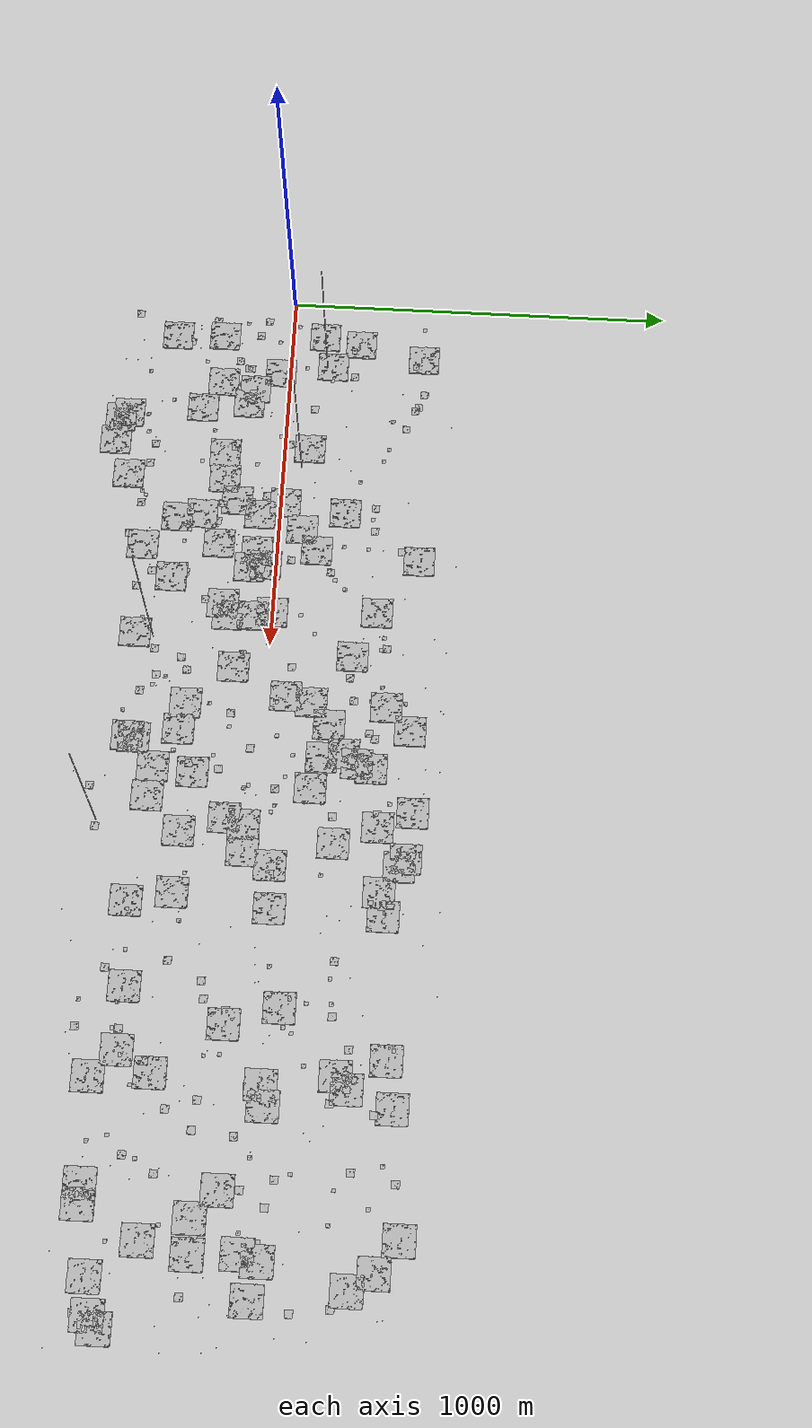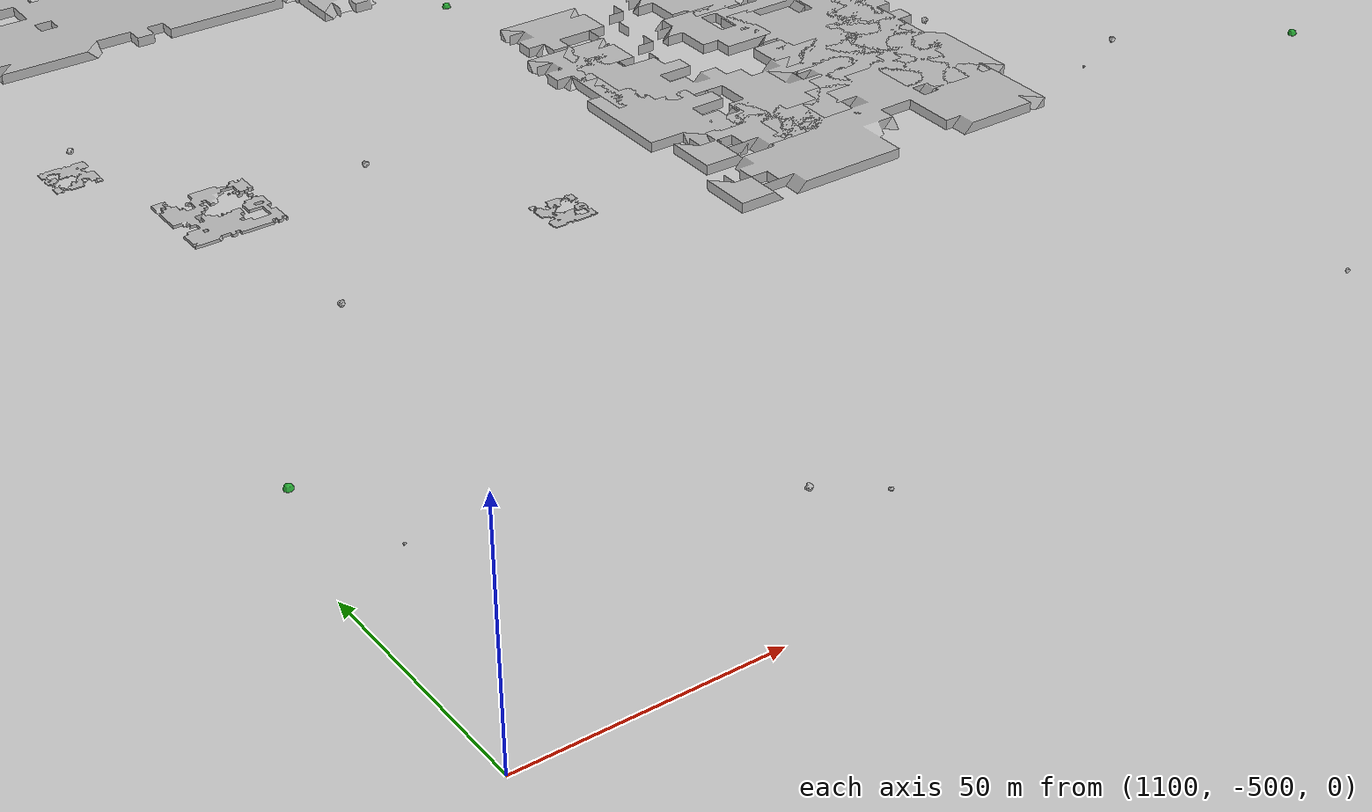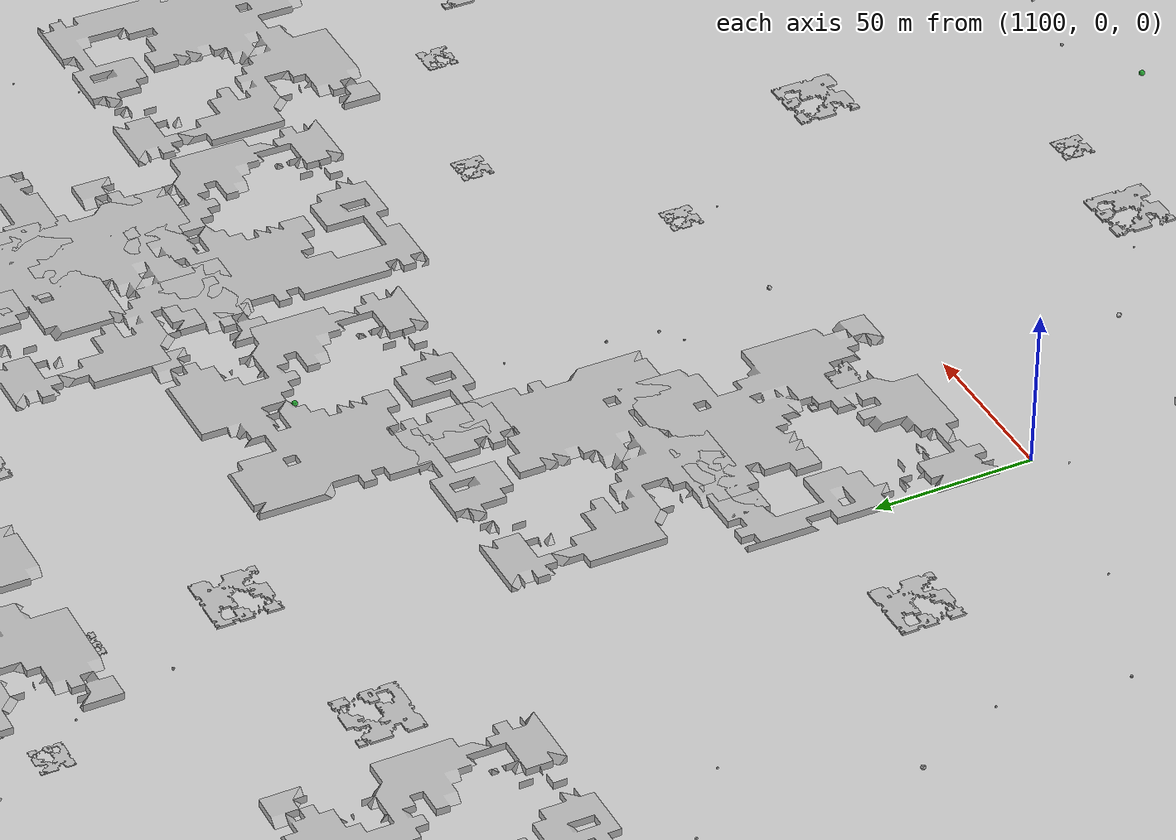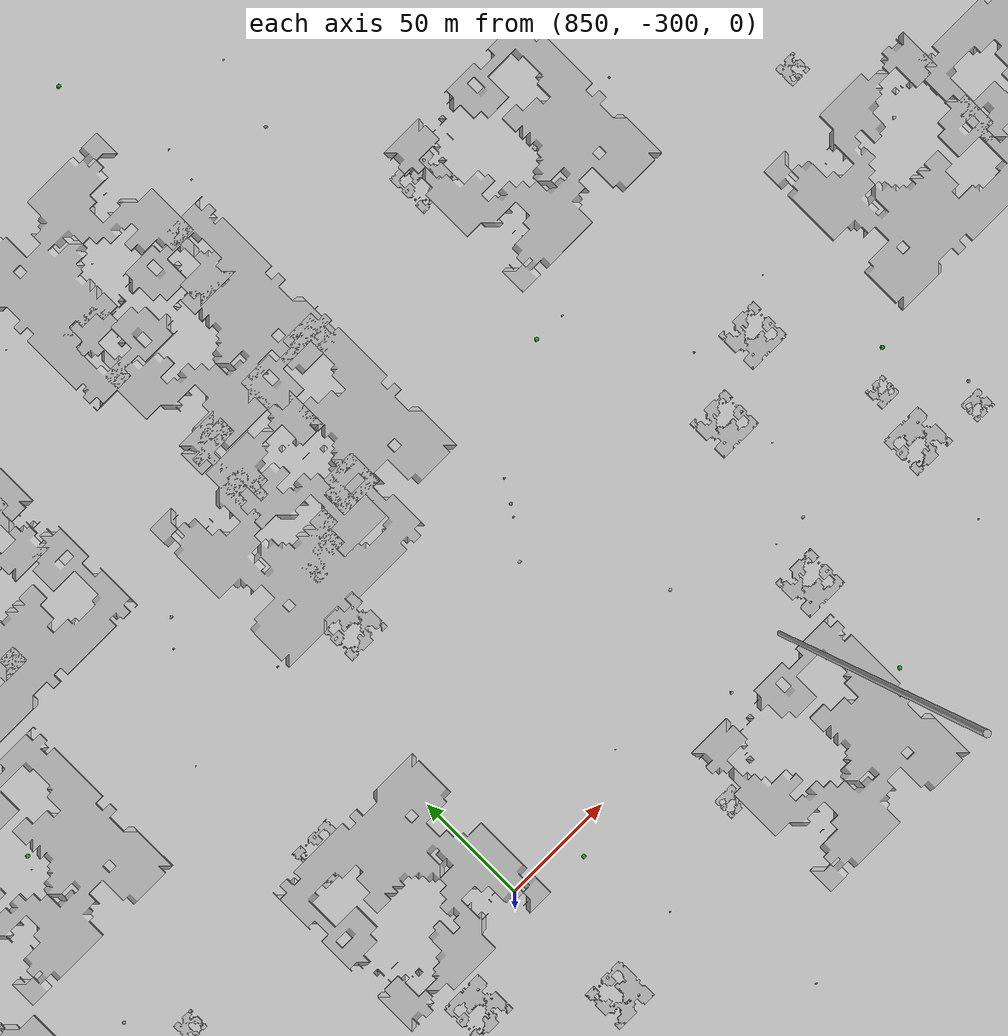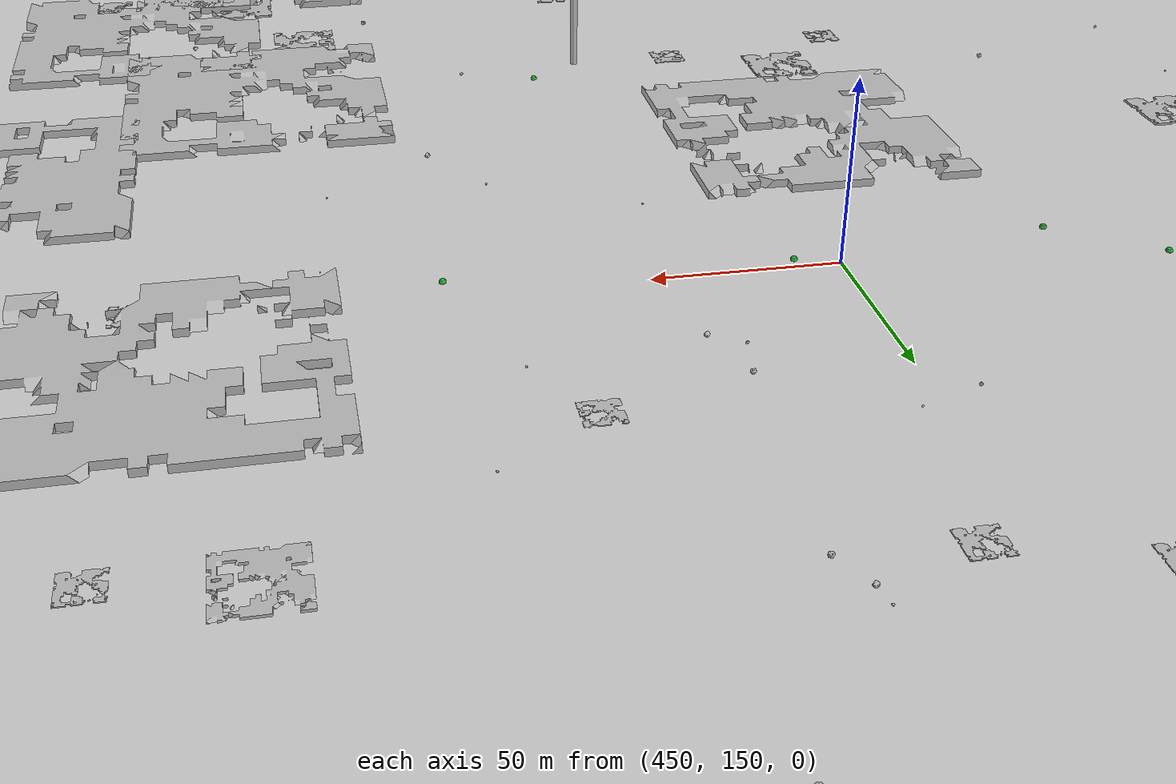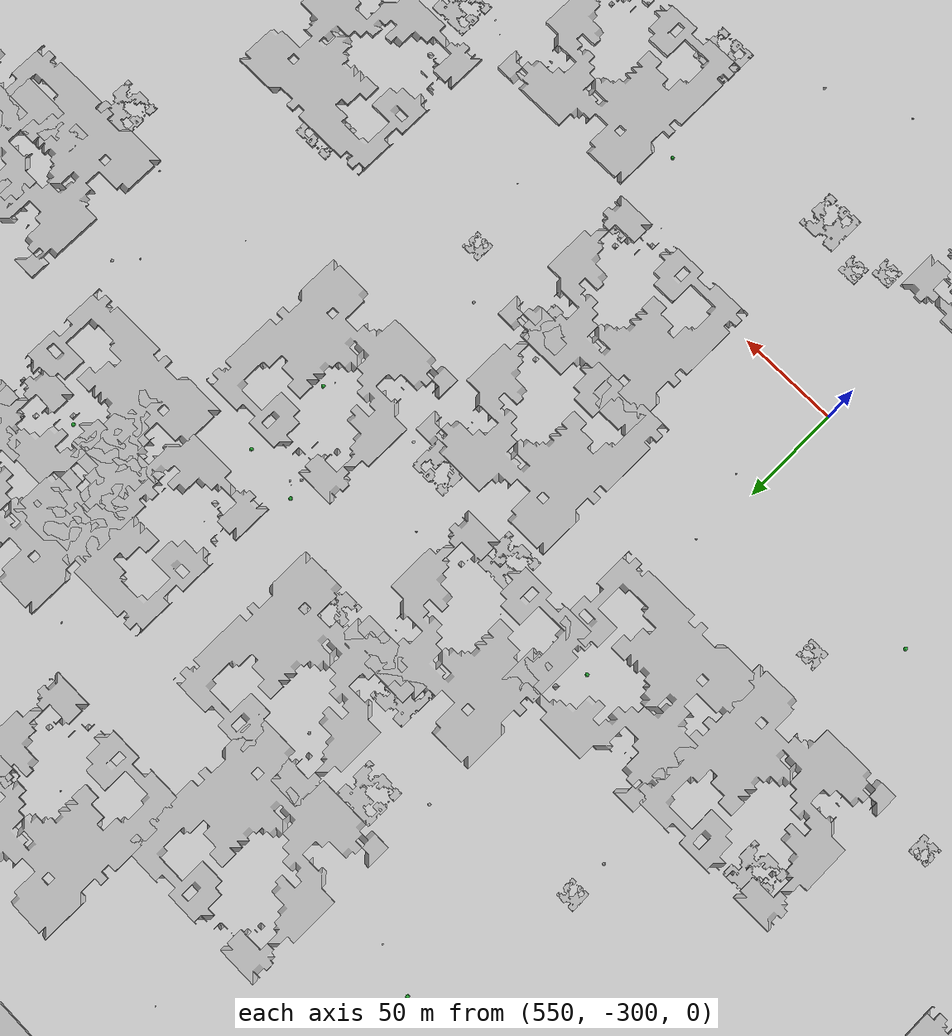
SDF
<?xml version="1.0" ?>
<sdf version="1.6">
  <world name="default">

    <include>
      <uri>model://sun</uri>
    </include>

    <include>
      <uri>model://custom_ground</uri>
    </include>

    <spherical_coordinates>
      <surface_model>EARTH_WGS84</surface_model>
      <latitude_deg>38.161479</latitude_deg>
      <longitude_deg>-122.454630</longitude_deg>
      <elevation>488.0</elevation>
      <heading_deg>90</heading_deg>
    </spherical_coordinates>

            <model name="hill1_1">
              <include>
                <uri>model://hill1</uri>
                <pose>646.11 -171.88 -1.6 0 0 1.5708</pose>
              </include>
            </model>

            <model name="hill1_2">
              <include>
                <uri>model://hill1</uri>
                <pose>2652.46 248.23 -1.6 0 0 1.5708</pose>
              </include>
            </model>

            <model name="hill1_3">
              <include>
                <uri>model://hill1</uri>
                <pose>712.33 336.51 -1.6 0 0 0.0</pose>
              </include>
            </model>

            <model name="hill1_4">
              <include>
                <uri>model://hill1</uri>
                <pose>1974.14 -50.71 -1.6 0 0 3.1416</pose>
              </include>
            </model>

            <model name="hill1_5">
              <include>
                <uri>model://hill1</uri>
                <pose>1379.64 49.59 -1.6 0 0 0.0</pose>
              </include>
            </model>

            <model name="hill1_6">
              <include>
                <uri>model://hill1</uri>
                <pose>2031.28 -307.78 -1.6 0 0 3.1416</pose>
              </include>
            </model>

            <model name="hill1_7">
              <include>
                <uri>model://hill1</uri>
                <pose>796.52 -244.69 -1.6 0 0 1.5708</pose>
              </include>
            </model>

            <model name="hill1_8">
              <include>
                <uri>model://hill1</uri>
                <pose>1976.79 229.73 -1.6 0 0 4.7124</pose>
              </include>
            </model>

            <model name="hill1_9">
              <include>
                <uri>model://hill1</uri>
                <pose>1855.77 -202.76 -1.6 0 0 3.1416</pose>
              </include>
            </model>

            <model name="hill1_10">
              <include>
                <uri>model://hill1</uri>
                <pose>1465.84 179.03 -1.6 0 0 3.1416</pose>
              </include>
            </model>

            <model name="hill1_11">
              <include>
                <uri>model://hill1</uri>
                <pose>2160.4 90.59 -1.6 0 0 0.0</pose>
              </include>
            </model>

            <model name="hill1_12">
              <include>
                <uri>model://hill1</uri>
                <pose>427.9 -354.59 -1.6 0 0 1.5708</pose>
              </include>
            </model>

            <model name="hill1_13">
              <include>
                <uri>model://hill1</uri>
                <pose>2523.14 -84.72 -1.6 0 0 3.1416</pose>
              </include>
            </model>

            <model name="hill1_14">
              <include>
                <uri>model://hill1</uri>
                <pose>1884.38 -95.45 -1.6 0 0 0.0</pose>
              </include>
            </model>

            <model name="hill1_15">
              <include>
                <uri>model://hill1</uri>
                <pose>840.28 -369.8 -1.6 0 0 1.5708</pose>
              </include>
            </model>

            <model name="hill1_16">
              <include>
                <uri>model://hill1</uri>
                <pose>2270.32 -110.58 -1.6 0 0 3.1416</pose>
              </include>
            </model>

            <model name="hill1_17">
              <include>
                <uri>model://hill1</uri>
                <pose>1928.01 -106.67 -1.6 0 0 1.5708</pose>
              </include>
            </model>

            <model name="hill1_18">
              <include>
                <uri>model://hill1</uri>
                <pose>351.48 -196.71 -1.6 0 0 4.7124</pose>
              </include>
            </model>

            <model name="hill1_19">
              <include>
                <uri>model://hill1</uri>
                <pose>1982.81 -6.47 -1.6 0 0 0.0</pose>
              </include>
            </model>

            <model name="hill1_20">
              <include>
                <uri>model://hill1</uri>
                <pose>2661.97 -87.95 -1.6 0 0 4.7124</pose>
              </include>
            </model>

            <model name="hill1_21">
              <include>
                <uri>model://hill1</uri>
                <pose>2316.76 -271.04 -1.6 0 0 1.5708</pose>
              </include>
            </model>

            <model name="hill1_22">
              <include>
                <uri>model://hill1</uri>
                <pose>305.29 62.34 -1.6 0 0 1.5708</pose>
              </include>
            </model>

            <model name="hill1_23">
              <include>
                <uri>model://hill1</uri>
                <pose>1131.43 -314.83 -1.6 0 0 0.0</pose>
              </include>
            </model>

            <model name="hill1_24">
              <include>
                <uri>model://hill1</uri>
                <pose>1353.83 -117.06 -1.6 0 0 3.1416</pose>
              </include>
            </model>

            <model name="hill1_25">
              <include>
                <uri>model://hill1</uri>
                <pose>306.15 -103.66 -1.6 0 0 3.1416</pose>
              </include>
            </model>

            <model name="hill1_26">
              <include>
                <uri>model://hill1</uri>
                <pose>211.1 -122.35 -1.6 0 0 3.1416</pose>
              </include>
            </model>

            <model name="hill1_27">
              <include>
                <uri>model://hill1</uri>
                <pose>485.06 -364.29 -1.6 0 0 1.5708</pose>
              </include>
            </model>

            <model name="hill1_28">
              <include>
                <uri>model://hill1</uri>
                <pose>2110.63 288.94 -1.6 0 0 0.0</pose>
              </include>
            </model>

            <model name="hill1_29">
              <include>
                <uri>model://hill1</uri>
                <pose>2406.77 15.12 -1.6 0 0 3.1416</pose>
              </include>
            </model>

            <model name="hill1_30">
              <include>
                <uri>model://hill1</uri>
                <pose>1147.23 44.75 -1.6 0 0 0.0</pose>
              </include>
            </model>

            <model name="hill1_31">
              <include>
                <uri>model://hill1</uri>
                <pose>1068.67 49.62 -1.6 0 0 3.1416</pose>
              </include>
            </model>

            <model name="hill1_32">
              <include>
                <uri>model://hill1</uri>
                <pose>2374.77 385.69 -1.6 0 0 3.1416</pose>
              </include>
            </model>

            <model name="hill1_33">
              <include>
                <uri>model://hill1</uri>
                <pose>606.73 -67.67 -1.6 0 0 4.7124</pose>
              </include>
            </model>

            <model name="hill1_34">
              <include>
                <uri>model://hill1</uri>
                <pose>815.55 -333.27 -1.6 0 0 3.1416</pose>
              </include>
            </model>

            <model name="hill1_35">
              <include>
                <uri>model://hill1</uri>
                <pose>2202.32 -177.76 -1.6 0 0 1.5708</pose>
              </include>
            </model>

            <model name="hill1_36">
              <include>
                <uri>model://hill1</uri>
                <pose>798.36 133.73 -1.6 0 0 3.1416</pose>
              </include>
            </model>

            <model name="hill1_37">
              <include>
                <uri>model://hill1</uri>
                <pose>1500.53 -394.75 -1.6 0 0 0.0</pose>
              </include>
            </model>

            <model name="hill1_38">
              <include>
                <uri>model://hill1</uri>
                <pose>2056.31 255.27 -1.6 0 0 3.1416</pose>
              </include>
            </model>

            <model name="hill1_39">
              <include>
                <uri>model://hill1</uri>
                <pose>50.11 -195.72 -1.6 0 0 0.0</pose>
              </include>
            </model>

            <model name="hill1_40">
              <include>
                <uri>model://hill1</uri>
                <pose>164.44 326.35 -1.6 0 0 1.5708</pose>
              </include>
            </model>

            <model name="hill1_41">
              <include>
                <uri>model://hill1</uri>
                <pose>2378.66 -171.91 -1.6 0 0 4.7124</pose>
              </include>
            </model>

            <model name="hill1_42">
              <include>
                <uri>model://hill1</uri>
                <pose>1413.44 -418.35 -1.6 0 0 4.7124</pose>
              </include>
            </model>

            <model name="hill1_43">
              <include>
                <uri>model://hill1</uri>
                <pose>286.91 360.52 -1.6 0 0 0.0</pose>
              </include>
            </model>

            <model name="hill1_44">
              <include>
                <uri>model://hill1</uri>
                <pose>90.28 -76.63 -1.6 0 0 0.0</pose>
              </include>
            </model>

            <model name="hill1_45">
              <include>
                <uri>model://hill1</uri>
                <pose>1454.4 310.78 -1.6 0 0 4.7124</pose>
              </include>
            </model>

            <model name="hill1_46">
              <include>
                <uri>model://hill1</uri>
                <pose>1254.62 294.17 -1.6 0 0 4.7124</pose>
              </include>
            </model>

            <model name="hill1_47">
              <include>
                <uri>model://hill1</uri>
                <pose>1035.41 -215.63 -1.6 0 0 0.0</pose>
              </include>
            </model>

            <model name="hill1_48">
              <include>
                <uri>model://hill1</uri>
                <pose>1014.13 -286.23 -1.6 0 0 0.0</pose>
              </include>
            </model>

            <model name="hill1_49">
              <include>
                <uri>model://hill1</uri>
                <pose>586.42 -48.14 -1.6 0 0 3.1416</pose>
              </include>
            </model>

            <model name="hill1_50">
              <include>
                <uri>model://hill1</uri>
                <pose>1005.63 291.65 -1.6 0 0 3.1416</pose>
              </include>
            </model>

            <model name="hill1_51">
              <include>
                <uri>model://hill1</uri>
                <pose>2192.54 345.14 -1.6 0 0 0.0</pose>
              </include>
            </model>

            <model name="hill1_52">
              <include>
                <uri>model://hill1</uri>
                <pose>297.86 351.77 -1.6 0 0 0.0</pose>
              </include>
            </model>

            <model name="hill1_53">
              <include>
                <uri>model://hill1</uri>
                <pose>2169.46 216.89 -1.6 0 0 1.5708</pose>
              </include>
            </model>

            <model name="hill1_54">
              <include>
                <uri>model://hill1</uri>
                <pose>2088.98 -219.07 -1.6 0 0 0.0</pose>
              </include>
            </model>

            <model name="hill1_55">
              <include>
                <uri>model://hill1</uri>
                <pose>65.72 -56.96 -1.6 0 0 4.7124</pose>
              </include>
            </model>

            <model name="hill1_56">
              <include>
                <uri>model://hill1</uri>
                <pose>2028.83 379.44 -1.6 0 0 0.0</pose>
              </include>
            </model>

            <model name="hill1_57">
              <include>
                <uri>model://hill1</uri>
                <pose>889.67 -187.24 -1.6 0 0 3.1416</pose>
              </include>
            </model>

            <model name="hill1_58">
              <include>
                <uri>model://hill1</uri>
                <pose>614.43 -161.83 -1.6 0 0 3.1416</pose>
              </include>
            </model>

            <model name="hill1_59">
              <include>
                <uri>model://hill1</uri>
                <pose>122.74 162.57 -1.6 0 0 1.5708</pose>
              </include>
            </model>

            <model name="hill1_60">
              <include>
                <uri>model://hill1</uri>
                <pose>1672.42 316.64 -1.6 0 0 1.5708</pose>
              </include>
            </model>

            <model name="hill1_61">
              <include>
                <uri>model://hill1</uri>
                <pose>1603.03 32.71 -1.6 0 0 1.5708</pose>
              </include>
            </model>

            <model name="hill1_62">
              <include>
                <uri>model://hill1</uri>
                <pose>211.13 -115.53 -1.6 0 0 3.1416</pose>
              </include>
            </model>

            <model name="hill1_63">
              <include>
                <uri>model://hill1</uri>
                <pose>125.18 363.8 -1.6 0 0 1.5708</pose>
              </include>
            </model>

            <model name="hill1_64">
              <include>
                <uri>model://hill1</uri>
                <pose>636.02 -91.63 -1.6 0 0 1.5708</pose>
              </include>
            </model>

            <model name="hill1_65">
              <include>
                <uri>model://hill1</uri>
                <pose>1341.15 -192.89 -1.6 0 0 3.1416</pose>
              </include>
            </model>

            <model name="hill1_66">
              <include>
                <uri>model://hill1</uri>
                <pose>2260.32 -7.56 -1.6 0 0 1.5708</pose>
              </include>
            </model>

            <model name="hill1_67">
              <include>
                <uri>model://hill1</uri>
                <pose>2690.57 -352.25 -1.6 0 0 1.5708</pose>
              </include>
            </model>

            <model name="hill1_68">
              <include>
                <uri>model://hill1</uri>
                <pose>446.07 -141.38 -1.6 0 0 3.1416</pose>
              </include>
            </model>

            <model name="hill1_69">
              <include>
                <uri>model://hill1</uri>
                <pose>1861.49 -335.18 -1.6 0 0 0.0</pose>
              </include>
            </model>

            <model name="hill1_70">
              <include>
                <uri>model://hill1</uri>
                <pose>2332.84 297.31 -1.6 0 0 0.0</pose>
              </include>
            </model>

            <model name="hill1_71">
              <include>
                <uri>model://hill1</uri>
                <pose>169.69 -146.81 -1.6 0 0 1.5708</pose>
              </include>
            </model>

            <model name="hill1_72">
              <include>
                <uri>model://hill1</uri>
                <pose>1274.61 -40.45 -1.6 0 0 1.5708</pose>
              </include>
            </model>

            <model name="hill1_73">
              <include>
                <uri>model://hill1</uri>
                <pose>2425.28 78.02 -1.6 0 0 1.5708</pose>
              </include>
            </model>

            <model name="hill1_74">
              <include>
                <uri>model://hill1</uri>
                <pose>1239.77 259.42 -1.6 0 0 3.1416</pose>
              </include>
            </model>

            <model name="hill1_75">
              <include>
                <uri>model://hill1</uri>
                <pose>2378.72 96.42 -1.6 0 0 3.1416</pose>
              </include>
            </model>

            <model name="hill1_76">
              <include>
                <uri>model://hill1</uri>
                <pose>1105.69 -296.75 -1.6 0 0 3.1416</pose>
              </include>
            </model>

            <model name="hill1_77">
              <include>
                <uri>model://hill1</uri>
                <pose>768.36 28.18 -1.6 0 0 3.1416</pose>
              </include>
            </model>

            <model name="hill1_78">
              <include>
                <uri>model://hill1</uri>
                <pose>867.98 274.16 -1.6 0 0 0.0</pose>
              </include>
            </model>

            <model name="hill1_79">
              <include>
                <uri>model://hill1</uri>
                <pose>1932.84 129.71 -1.6 0 0 4.7124</pose>
              </include>
            </model>

            <model name="hill1_80">
              <include>
                <uri>model://hill1</uri>
                <pose>412.86 2.85 -1.6 0 0 1.5708</pose>
              </include>
            </model>

            <model name="hill1_81">
              <include>
                <uri>model://hill1</uri>
                <pose>675.68 262.68 -1.6 0 0 4.7124</pose>
              </include>
            </model>

            <model name="hill1_82">
              <include>
                <uri>model://hill1</uri>
                <pose>116.43 -281.63 -1.6 0 0 1.5708</pose>
              </include>
            </model>

            <model name="hill1_83">
              <include>
                <uri>model://hill1</uri>
                <pose>2011.46 -394.63 -1.6 0 0 0.0</pose>
              </include>
            </model>

            <model name="hill1_84">
              <include>
                <uri>model://hill1</uri>
                <pose>1039.1 -79.03 -1.6 0 0 3.1416</pose>
              </include>
            </model>

            <model name="hill1_85">
              <include>
                <uri>model://hill1</uri>
                <pose>653.37 -250.37 -1.6 0 0 1.5708</pose>
              </include>
            </model>

            <model name="hill1_86">
              <include>
                <uri>model://hill1</uri>
                <pose>2138.81 16.42 -1.6 0 0 1.5708</pose>
              </include>
            </model>

            <model name="hill1_87">
              <include>
                <uri>model://hill1</uri>
                <pose>1153.02 215.11 -1.6 0 0 3.1416</pose>
              </include>
            </model>

            <model name="hill1_88">
              <include>
                <uri>model://hill1</uri>
                <pose>1069.07 -198.51 -1.6 0 0 0.0</pose>
              </include>
            </model>

            <model name="hill1_89">
              <include>
                <uri>model://hill1</uri>
                <pose>2176.86 -102.07 -1.6 0 0 1.5708</pose>
              </include>
            </model>

            <model name="hill1_90">
              <include>
                <uri>model://hill1</uri>
                <pose>203.44 183.47 -1.6 0 0 0.0</pose>
              </include>
            </model>

            <model name="hill1_91">
              <include>
                <uri>model://hill1</uri>
                <pose>712.77 -382.77 -1.6 0 0 4.7124</pose>
              </include>
            </model>

            <model name="hill1_92">
              <include>
                <uri>model://hill1</uri>
                <pose>247.82 353.86 -1.6 0 0 1.5708</pose>
              </include>
            </model>

            <model name="hill1_93">
              <include>
                <uri>model://hill1</uri>
                <pose>1071.64 221.42 -1.6 0 0 0.0</pose>
              </include>
            </model>

            <model name="hill1_94">
              <include>
                <uri>model://hill1</uri>
                <pose>1818.32 207.36 -1.6 0 0 1.5708</pose>
              </include>
            </model>

            <model name="hill1_95">
              <include>
                <uri>model://hill1</uri>
                <pose>589.89 261.45 -1.6 0 0 0.0</pose>
              </include>
            </model>

            <model name="hill1_96">
              <include>
                <uri>model://hill1</uri>
                <pose>1181.92 -96.58 -1.6 0 0 1.5708</pose>
              </include>
            </model>

            <model name="hill1_97">
              <include>
                <uri>model://hill1</uri>
                <pose>373.32 329.3 -1.6 0 0 4.7124</pose>
              </include>
            </model>

            <model name="hill1_98">
              <include>
                <uri>model://hill1</uri>
                <pose>621.85 -358.06 -1.6 0 0 4.7124</pose>
              </include>
            </model>

            <model name="hill1_99">
              <include>
                <uri>model://hill1</uri>
                <pose>58.24 -408.23 -1.6 0 0 4.7124</pose>
              </include>
            </model>

            <model name="hill1_100">
              <include>
                <uri>model://hill1</uri>
                <pose>2686.96 151.94 -1.6 0 0 3.1416</pose>
              </include>
            </model>

            <model name="hill2_1">
              <include>
                <uri>model://hill2</uri>
                <pose>2035.23 -256.57 -6 0 0 0.0</pose>
              </include>
            </model>

            <model name="hill2_2">
              <include>
                <uri>model://hill2</uri>
                <pose>75.29 226.64 -6 0 0 0.0</pose>
              </include>
            </model>

            <model name="hill2_3">
              <include>
                <uri>model://hill2</uri>
                <pose>1990.94 49.49 -6 0 0 3.1416</pose>
              </include>
            </model>

            <model name="hill2_4">
              <include>
                <uri>model://hill2</uri>
                <pose>553.74 -27.27 -6 0 0 1.5708</pose>
              </include>
            </model>

            <model name="hill2_5">
              <include>
                <uri>model://hill2</uri>
                <pose>1486.77 235.88 -6 0 0 0.0</pose>
              </include>
            </model>

            <model name="hill2_6">
              <include>
                <uri>model://hill2</uri>
                <pose>1383.55 -240.54 -6 0 0 0.0</pose>
              </include>
            </model>

            <model name="hill2_7">
              <include>
                <uri>model://hill2</uri>
                <pose>489.44 -367.93 -6 0 0 0.0</pose>
              </include>
            </model>

            <model name="hill2_8">
              <include>
                <uri>model://hill2</uri>
                <pose>768.55 142.8 -6 0 0 4.7124</pose>
              </include>
            </model>

            <model name="hill2_9">
              <include>
                <uri>model://hill2</uri>
                <pose>1394.63 -212.43 -6 0 0 3.1416</pose>
              </include>
            </model>

            <model name="hill2_10">
              <include>
                <uri>model://hill2</uri>
                <pose>2535.97 370.76 -6 0 0 3.1416</pose>
              </include>
            </model>

            <model name="hill2_11">
              <include>
                <uri>model://hill2</uri>
                <pose>1024.55 -129.33 -6 0 0 1.5708</pose>
              </include>
            </model>

            <model name="hill2_12">
              <include>
                <uri>model://hill2</uri>
                <pose>1596.15 -71.16 -6 0 0 3.1416</pose>
              </include>
            </model>

            <model name="hill2_13">
              <include>
                <uri>model://hill2</uri>
                <pose>2360.5 14.15 -6 0 0 0.0</pose>
              </include>
            </model>

            <model name="hill2_14">
              <include>
                <uri>model://hill2</uri>
                <pose>949.16 38.05 -6 0 0 4.7124</pose>
              </include>
            </model>

            <model name="hill2_15">
              <include>
                <uri>model://hill2</uri>
                <pose>1539.23 324.15 -6 0 0 1.5708</pose>
              </include>
            </model>

            <model name="hill2_16">
              <include>
                <uri>model://hill2</uri>
                <pose>1476.23 349.73 -6 0 0 3.1416</pose>
              </include>
            </model>

            <model name="hill2_17">
              <include>
                <uri>model://hill2</uri>
                <pose>2108.88 317.67 -6 0 0 3.1416</pose>
              </include>
            </model>

            <model name="hill2_18">
              <include>
                <uri>model://hill2</uri>
                <pose>2439.81 -316.06 -6 0 0 4.7124</pose>
              </include>
            </model>

            <model name="hill2_19">
              <include>
                <uri>model://hill2</uri>
                <pose>2427.88 -127.04 -6 0 0 1.5708</pose>
              </include>
            </model>

            <model name="hill2_20">
              <include>
                <uri>model://hill2</uri>
                <pose>1748.42 290.08 -6 0 0 3.1416</pose>
              </include>
            </model>

            <model name="hill2_21">
              <include>
                <uri>model://hill2</uri>
                <pose>1446.36 -71.64 -6 0 0 1.5708</pose>
              </include>
            </model>

            <model name="hill2_22">
              <include>
                <uri>model://hill2</uri>
                <pose>775.94 -93.64 -6 0 0 3.1416</pose>
              </include>
            </model>

            <model name="hill2_23">
              <include>
                <uri>model://hill2</uri>
                <pose>205.07 -136.63 -6 0 0 0.0</pose>
              </include>
            </model>

            <model name="hill2_24">
              <include>
                <uri>model://hill2</uri>
                <pose>816.64 12.21 -6 0 0 4.7124</pose>
              </include>
            </model>

            <model name="hill2_25">
              <include>
                <uri>model://hill2</uri>
                <pose>324.32 -403.02 -6 0 0 0.0</pose>
              </include>
            </model>

            <model name="hill2_26">
              <include>
                <uri>model://hill2</uri>
                <pose>135.68 46.42 -6 0 0 3.1416</pose>
              </include>
            </model>

            <model name="hill2_27">
              <include>
                <uri>model://hill2</uri>
                <pose>251.03 13.77 -6 0 0 4.7124</pose>
              </include>
            </model>

            <model name="hill2_28">
              <include>
                <uri>model://hill2</uri>
                <pose>1178.45 9.96 -6 0 0 3.1416</pose>
              </include>
            </model>

            <model name="hill2_29">
              <include>
                <uri>model://hill2</uri>
                <pose>113.51 397.84 -6 0 0 0.0</pose>
              </include>
            </model>

            <model name="hill2_30">
              <include>
                <uri>model://hill2</uri>
                <pose>2520.65 40.67 -6 0 0 1.5708</pose>
              </include>
            </model>

            <model name="hill2_31">
              <include>
                <uri>model://hill2</uri>
                <pose>850.34 -89.99 -6 0 0 0.0</pose>
              </include>
            </model>

            <model name="hill2_32">
              <include>
                <uri>model://hill2</uri>
                <pose>678.51 -193.25 -6 0 0 1.5708</pose>
              </include>
            </model>

            <model name="hill2_33">
              <include>
                <uri>model://hill2</uri>
                <pose>2693.79 101.45 -6 0 0 4.7124</pose>
              </include>
            </model>

            <model name="hill2_34">
              <include>
                <uri>model://hill2</uri>
                <pose>309.01 -382.27 -6 0 0 0.0</pose>
              </include>
            </model>

            <model name="hill2_35">
              <include>
                <uri>model://hill2</uri>
                <pose>415.59 -196.7 -6 0 0 1.5708</pose>
              </include>
            </model>

            <model name="hill2_36">
              <include>
                <uri>model://hill2</uri>
                <pose>1284.91 320.24 -6 0 0 0.0</pose>
              </include>
            </model>

            <model name="hill2_37">
              <include>
                <uri>model://hill2</uri>
                <pose>881.48 -154.3 -6 0 0 1.5708</pose>
              </include>
            </model>

            <model name="hill2_38">
              <include>
                <uri>model://hill2</uri>
                <pose>2587.45 70.94 -6 0 0 4.7124</pose>
              </include>
            </model>

            <model name="hill2_39">
              <include>
                <uri>model://hill2</uri>
                <pose>656.76 131.63 -6 0 0 3.1416</pose>
              </include>
            </model>

            <model name="hill2_40">
              <include>
                <uri>model://hill2</uri>
                <pose>1342.82 89.29 -6 0 0 1.5708</pose>
              </include>
            </model>

            <model name="hill2_41">
              <include>
                <uri>model://hill2</uri>
                <pose>392.28 -411.17 -6 0 0 0.0</pose>
              </include>
            </model>

            <model name="hill2_42">
              <include>
                <uri>model://hill2</uri>
                <pose>744.79 -28.17 -6 0 0 0.0</pose>
              </include>
            </model>

            <model name="hill2_43">
              <include>
                <uri>model://hill2</uri>
                <pose>2692.78 -327.6 -6 0 0 1.5708</pose>
              </include>
            </model>

            <model name="hill2_44">
              <include>
                <uri>model://hill2</uri>
                <pose>1224.95 -384.98 -6 0 0 1.5708</pose>
              </include>
            </model>

            <model name="hill2_45">
              <include>
                <uri>model://hill2</uri>
                <pose>2103.87 98.5 -6 0 0 0.0</pose>
              </include>
            </model>

            <model name="hill2_46">
              <include>
                <uri>model://hill2</uri>
                <pose>2225.46 337.86 -6 0 0 3.1416</pose>
              </include>
            </model>

            <model name="hill2_47">
              <include>
                <uri>model://hill2</uri>
                <pose>1062.72 253.95 -6 0 0 4.7124</pose>
              </include>
            </model>

            <model name="hill2_48">
              <include>
                <uri>model://hill2</uri>
                <pose>2576.19 -282.63 -6 0 0 0.0</pose>
              </include>
            </model>

            <model name="hill2_49">
              <include>
                <uri>model://hill2</uri>
                <pose>2593.02 -126.83 -6 0 0 3.1416</pose>
              </include>
            </model>

            <model name="hill2_50">
              <include>
                <uri>model://hill2</uri>
                <pose>2536.03 396.2 -6 0 0 0.0</pose>
              </include>
            </model>

            <model name="hill2_51">
              <include>
                <uri>model://hill2</uri>
                <pose>1439.79 344.78 -6 0 0 0.0</pose>
              </include>
            </model>

            <model name="hill2_52">
              <include>
                <uri>model://hill2</uri>
                <pose>1631.48 -236.16 -6 0 0 1.5708</pose>
              </include>
            </model>

            <model name="hill2_53">
              <include>
                <uri>model://hill2</uri>
                <pose>1609.16 357.31 -6 0 0 0.0</pose>
              </include>
            </model>

            <model name="hill2_54">
              <include>
                <uri>model://hill2</uri>
                <pose>1340.24 191.4 -6 0 0 4.7124</pose>
              </include>
            </model>

            <model name="hill2_55">
              <include>
                <uri>model://hill2</uri>
                <pose>772.91 -313.7 -6 0 0 4.7124</pose>
              </include>
            </model>

            <model name="hill2_56">
              <include>
                <uri>model://hill2</uri>
                <pose>1252.11 204.97 -6 0 0 4.7124</pose>
              </include>
            </model>

            <model name="hill2_57">
              <include>
                <uri>model://hill2</uri>
                <pose>1178.6 333.53 -6 0 0 1.5708</pose>
              </include>
            </model>

            <model name="hill2_58">
              <include>
                <uri>model://hill2</uri>
                <pose>2038.18 -83.74 -6 0 0 3.1416</pose>
              </include>
            </model>

            <model name="hill2_59">
              <include>
                <uri>model://hill2</uri>
                <pose>940.31 -390.36 -6 0 0 1.5708</pose>
              </include>
            </model>

            <model name="hill2_60">
              <include>
                <uri>model://hill2</uri>
                <pose>1659.48 -268.81 -6 0 0 0.0</pose>
              </include>
            </model>

            <model name="hill2_61">
              <include>
                <uri>model://hill2</uri>
                <pose>393.73 107.56 -6 0 0 0.0</pose>
              </include>
            </model>

            <model name="hill2_62">
              <include>
                <uri>model://hill2</uri>
                <pose>1246.7 168.02 -6 0 0 1.5708</pose>
              </include>
            </model>

            <model name="hill2_63">
              <include>
                <uri>model://hill2</uri>
                <pose>267.32 -63.74 -6 0 0 0.0</pose>
              </include>
            </model>

            <model name="hill2_64">
              <include>
                <uri>model://hill2</uri>
                <pose>1228.47 -367.89 -6 0 0 1.5708</pose>
              </include>
            </model>

            <model name="hill2_65">
              <include>
                <uri>model://hill2</uri>
                <pose>709.95 101.04 -6 0 0 4.7124</pose>
              </include>
            </model>

            <model name="hill2_66">
              <include>
                <uri>model://hill2</uri>
                <pose>1111.59 77.31 -6 0 0 1.5708</pose>
              </include>
            </model>

            <model name="hill2_67">
              <include>
                <uri>model://hill2</uri>
                <pose>1129.87 -163.98 -6 0 0 0.0</pose>
              </include>
            </model>

            <model name="hill2_68">
              <include>
                <uri>model://hill2</uri>
                <pose>1551.48 81.75 -6 0 0 0.0</pose>
              </include>
            </model>

            <model name="hill2_69">
              <include>
                <uri>model://hill2</uri>
                <pose>1273.96 283.0 -6 0 0 0.0</pose>
              </include>
            </model>

            <model name="hill2_70">
              <include>
                <uri>model://hill2</uri>
                <pose>1876.63 -252.55 -6 0 0 0.0</pose>
              </include>
            </model>

            <model name="hill2_71">
              <include>
                <uri>model://hill2</uri>
                <pose>2407.73 -394.21 -6 0 0 1.5708</pose>
              </include>
            </model>

            <model name="hill2_72">
              <include>
                <uri>model://hill2</uri>
                <pose>859.7 -311.17 -6 0 0 3.1416</pose>
              </include>
            </model>

            <model name="hill2_73">
              <include>
                <uri>model://hill2</uri>
                <pose>2665.15 -267.46 -6 0 0 0.0</pose>
              </include>
            </model>

            <model name="hill2_74">
              <include>
                <uri>model://hill2</uri>
                <pose>2579.65 334.84 -6 0 0 0.0</pose>
              </include>
            </model>

            <model name="hill2_75">
              <include>
                <uri>model://hill2</uri>
                <pose>879.79 -89.39 -6 0 0 1.5708</pose>
              </include>
            </model>

            <model name="hill2_76">
              <include>
                <uri>model://hill2</uri>
                <pose>1280.95 -257.68 -6 0 0 3.1416</pose>
              </include>
            </model>

            <model name="hill2_77">
              <include>
                <uri>model://hill2</uri>
                <pose>688.8 -229.39 -6 0 0 4.7124</pose>
              </include>
            </model>

            <model name="hill2_78">
              <include>
                <uri>model://hill2</uri>
                <pose>1472.73 -153.36 -6 0 0 0.0</pose>
              </include>
            </model>

            <model name="hill2_79">
              <include>
                <uri>model://hill2</uri>
                <pose>2234.88 106.16 -6 0 0 4.7124</pose>
              </include>
            </model>

            <model name="hill2_80">
              <include>
                <uri>model://hill2</uri>
                <pose>2486.89 -165.31 -6 0 0 0.0</pose>
              </include>
            </model>

            <model name="hill2_81">
              <include>
                <uri>model://hill2</uri>
                <pose>676.97 -165.44 -6 0 0 4.7124</pose>
              </include>
            </model>

            <model name="hill2_82">
              <include>
                <uri>model://hill2</uri>
                <pose>2102.65 -320.83 -6 0 0 0.0</pose>
              </include>
            </model>

            <model name="hill2_83">
              <include>
                <uri>model://hill2</uri>
                <pose>785.75 332.29 -6 0 0 3.1416</pose>
              </include>
            </model>

            <model name="hill2_84">
              <include>
                <uri>model://hill2</uri>
                <pose>858.04 311.76 -6 0 0 0.0</pose>
              </include>
            </model>

            <model name="hill2_85">
              <include>
                <uri>model://hill2</uri>
                <pose>2073.43 277.74 -6 0 0 0.0</pose>
              </include>
            </model>

            <model name="hill2_86">
              <include>
                <uri>model://hill2</uri>
                <pose>491.53 -111.97 -6 0 0 0.0</pose>
              </include>
            </model>

            <model name="hill2_87">
              <include>
                <uri>model://hill2</uri>
                <pose>363.36 -267.51 -6 0 0 3.1416</pose>
              </include>
            </model>

            <model name="hill2_88">
              <include>
                <uri>model://hill2</uri>
                <pose>1517.78 339.31 -6 0 0 1.5708</pose>
              </include>
            </model>

            <model name="hill2_89">
              <include>
                <uri>model://hill2</uri>
                <pose>224.89 73.4 -6 0 0 3.1416</pose>
              </include>
            </model>

            <model name="hill2_90">
              <include>
                <uri>model://hill2</uri>
                <pose>148.45 -351.63 -6 0 0 3.1416</pose>
              </include>
            </model>

            <model name="hill2_91">
              <include>
                <uri>model://hill2</uri>
                <pose>1511.47 -122.77 -6 0 0 3.1416</pose>
              </include>
            </model>

            <model name="hill2_92">
              <include>
                <uri>model://hill2</uri>
                <pose>302.3 -131.69 -6 0 0 3.1416</pose>
              </include>
            </model>

            <model name="hill2_93">
              <include>
                <uri>model://hill2</uri>
                <pose>634.48 -75.96 -6 0 0 4.7124</pose>
              </include>
            </model>

            <model name="hill2_94">
              <include>
                <uri>model://hill2</uri>
                <pose>1116.69 269.73 -6 0 0 1.5708</pose>
              </include>
            </model>

            <model name="hill2_95">
              <include>
                <uri>model://hill2</uri>
                <pose>1304.11 -312.92 -6 0 0 1.5708</pose>
              </include>
            </model>

            <model name="hill2_96">
              <include>
                <uri>model://hill2</uri>
                <pose>145.71 -144.59 -6 0 0 4.7124</pose>
              </include>
            </model>

            <model name="hill2_97">
              <include>
                <uri>model://hill2</uri>
                <pose>1741.73 7.02 -6 0 0 3.1416</pose>
              </include>
            </model>

            <model name="hill2_98">
              <include>
                <uri>model://hill2</uri>
                <pose>2166.08 -251.91 -6 0 0 3.1416</pose>
              </include>
            </model>

            <model name="hill2_99">
              <include>
                <uri>model://hill2</uri>
                <pose>590.76 -91.05 -6 0 0 1.5708</pose>
              </include>
            </model>

            <model name="hill2_100">
              <include>
                <uri>model://hill2</uri>
                <pose>2183.28 225.22 -6 0 0 3.1416</pose>
              </include>
            </model>

            <model name="hill3_1">
              <include>
                <uri>model://hill3</uri>
                <pose>1147.11 275.84 -1 0 0 4.7124</pose>
              </include>
            </model>

            <model name="hill3_2">
              <include>
                <uri>model://hill3</uri>
                <pose>1829.91 -293.81 -1 0 0 4.7124</pose>
              </include>
            </model>

            <model name="hill3_3">
              <include>
                <uri>model://hill3</uri>
                <pose>2464.01 246.44 -1 0 0 0.0</pose>
              </include>
            </model>

            <model name="hill3_4">
              <include>
                <uri>model://hill3</uri>
                <pose>2318.53 367.89 -1 0 0 0.0</pose>
              </include>
            </model>

            <model name="hill3_5">
              <include>
                <uri>model://hill3</uri>
                <pose>1931.28 221.79 -1 0 0 0.0</pose>
              </include>
            </model>

            <model name="hill3_6">
              <include>
                <uri>model://hill3</uri>
                <pose>2129.25 68.33 -1 0 0 4.7124</pose>
              </include>
            </model>

            <model name="hill3_7">
              <include>
                <uri>model://hill3</uri>
                <pose>1739.45 -168.45 -1 0 0 0.0</pose>
              </include>
            </model>

            <model name="hill3_8">
              <include>
                <uri>model://hill3</uri>
                <pose>462.35 -7.3 -1 0 0 3.1416</pose>
              </include>
            </model>

            <model name="hill3_9">
              <include>
                <uri>model://hill3</uri>
                <pose>2068.17 -41.71 -1 0 0 0.0</pose>
              </include>
            </model>

            <model name="hill3_10">
              <include>
                <uri>model://hill3</uri>
                <pose>2391.19 254.41 -1 0 0 4.7124</pose>
              </include>
            </model>

            <model name="hill3_11">
              <include>
                <uri>model://hill3</uri>
                <pose>1626.35 -174.03 -1 0 0 3.1416</pose>
              </include>
            </model>

            <model name="hill3_12">
              <include>
                <uri>model://hill3</uri>
                <pose>593.84 -363.84 -1 0 0 3.1416</pose>
              </include>
            </model>

            <model name="hill3_13">
              <include>
                <uri>model://hill3</uri>
                <pose>1098.47 301.04 -1 0 0 0.0</pose>
              </include>
            </model>

            <model name="hill3_14">
              <include>
                <uri>model://hill3</uri>
                <pose>1192.24 -358.97 -1 0 0 0.0</pose>
              </include>
            </model>

            <model name="hill3_15">
              <include>
                <uri>model://hill3</uri>
                <pose>420.18 271.78 -1 0 0 1.5708</pose>
              </include>
            </model>

            <model name="hill3_16">
              <include>
                <uri>model://hill3</uri>
                <pose>718.87 169.01 -1 0 0 3.1416</pose>
              </include>
            </model>

            <model name="hill3_17">
              <include>
                <uri>model://hill3</uri>
                <pose>1116.82 304.24 -1 0 0 1.5708</pose>
              </include>
            </model>

            <model name="hill3_18">
              <include>
                <uri>model://hill3</uri>
                <pose>1303.06 204.3 -1 0 0 4.7124</pose>
              </include>
            </model>

            <model name="hill3_19">
              <include>
                <uri>model://hill3</uri>
                <pose>2073.69 -80.23 -1 0 0 0.0</pose>
              </include>
            </model>

            <model name="hill3_20">
              <include>
                <uri>model://hill3</uri>
                <pose>627.6 241.66 -1 0 0 1.5708</pose>
              </include>
            </model>

            <model name="hill3_21">
              <include>
                <uri>model://hill3</uri>
                <pose>2286.65 -296.19 -1 0 0 4.7124</pose>
              </include>
            </model>

            <model name="hill3_22">
              <include>
                <uri>model://hill3</uri>
                <pose>346.64 278.5 -1 0 0 3.1416</pose>
              </include>
            </model>

            <model name="hill3_23">
              <include>
                <uri>model://hill3</uri>
                <pose>2016.09 -317.91 -1 0 0 1.5708</pose>
              </include>
            </model>

            <model name="hill3_24">
              <include>
                <uri>model://hill3</uri>
                <pose>197.38 38.49 -1 0 0 3.1416</pose>
              </include>
            </model>

            <model name="hill3_25">
              <include>
                <uri>model://hill3</uri>
                <pose>490.28 -64.74 -1 0 0 4.7124</pose>
              </include>
            </model>

            <model name="hill3_26">
              <include>
                <uri>model://hill3</uri>
                <pose>2510.28 73.68 -1 0 0 1.5708</pose>
              </include>
            </model>

            <model name="hill3_27">
              <include>
                <uri>model://hill3</uri>
                <pose>1446.58 39.1 -1 0 0 0.0</pose>
              </include>
            </model>

            <model name="hill3_28">
              <include>
                <uri>model://hill3</uri>
                <pose>2596.4 -352.06 -1 0 0 4.7124</pose>
              </include>
            </model>

            <model name="hill3_29">
              <include>
                <uri>model://hill3</uri>
                <pose>345.87 -375.76 -1 0 0 1.5708</pose>
              </include>
            </model>

            <model name="hill3_30">
              <include>
                <uri>model://hill3</uri>
                <pose>1429.22 47.25 -1 0 0 0.0</pose>
              </include>
            </model>

            <model name="hill3_31">
              <include>
                <uri>model://hill3</uri>
                <pose>2007.78 128.55 -1 0 0 0.0</pose>
              </include>
            </model>

            <model name="hill3_32">
              <include>
                <uri>model://hill3</uri>
                <pose>1094.95 -257.1 -1 0 0 0.0</pose>
              </include>
            </model>

            <model name="hill3_33">
              <include>
                <uri>model://hill3</uri>
                <pose>2535.4 47.02 -1 0 0 3.1416</pose>
              </include>
            </model>

            <model name="hill3_34">
              <include>
                <uri>model://hill3</uri>
                <pose>815.61 151.17 -1 0 0 3.1416</pose>
              </include>
            </model>

            <model name="hill3_35">
              <include>
                <uri>model://hill3</uri>
                <pose>581.85 -373.5 -1 0 0 3.1416</pose>
              </include>
            </model>

            <model name="hill3_36">
              <include>
                <uri>model://hill3</uri>
                <pose>2081.66 -282.18 -1 0 0 0.0</pose>
              </include>
            </model>

            <model name="hill3_37">
              <include>
                <uri>model://hill3</uri>
                <pose>245.56 -134.51 -1 0 0 1.5708</pose>
              </include>
            </model>

            <model name="hill3_38">
              <include>
                <uri>model://hill3</uri>
                <pose>1844.02 53.28 -1 0 0 1.5708</pose>
              </include>
            </model>

            <model name="hill3_39">
              <include>
                <uri>model://hill3</uri>
                <pose>1725.61 -309.23 -1 0 0 3.1416</pose>
              </include>
            </model>

            <model name="hill3_40">
              <include>
                <uri>model://hill3</uri>
                <pose>310.84 -301.26 -1 0 0 4.7124</pose>
              </include>
            </model>

            <model name="hill3_41">
              <include>
                <uri>model://hill3</uri>
                <pose>66.29 361.16 -1 0 0 4.7124</pose>
              </include>
            </model>

            <model name="hill3_42">
              <include>
                <uri>model://hill3</uri>
                <pose>398.19 -361.07 -1 0 0 0.0</pose>
              </include>
            </model>

            <model name="hill3_43">
              <include>
                <uri>model://hill3</uri>
                <pose>1532.08 366.99 -1 0 0 0.0</pose>
              </include>
            </model>

            <model name="hill3_44">
              <include>
                <uri>model://hill3</uri>
                <pose>968.08 108.14 -1 0 0 3.1416</pose>
              </include>
            </model>

            <model name="hill3_45">
              <include>
                <uri>model://hill3</uri>
                <pose>1172.24 -138.6 -1 0 0 4.7124</pose>
              </include>
            </model>

            <model name="hill3_46">
              <include>
                <uri>model://hill3</uri>
                <pose>1961.33 -301.06 -1 0 0 4.7124</pose>
              </include>
            </model>

            <model name="hill3_47">
              <include>
                <uri>model://hill3</uri>
                <pose>2507.81 -102.61 -1 0 0 3.1416</pose>
              </include>
            </model>

            <model name="hill3_48">
              <include>
                <uri>model://hill3</uri>
                <pose>1222.96 -93.14 -1 0 0 1.5708</pose>
              </include>
            </model>

            <model name="hill3_49">
              <include>
                <uri>model://hill3</uri>
                <pose>2502.95 36.01 -1 0 0 4.7124</pose>
              </include>
            </model>

            <model name="hill3_50">
              <include>
                <uri>model://hill3</uri>
                <pose>633.22 148.9 -1 0 0 4.7124</pose>
              </include>
            </model>

            <model name="hill3_51">
              <include>
                <uri>model://hill3</uri>
                <pose>1304.88 -220.0 -1 0 0 4.7124</pose>
              </include>
            </model>

            <model name="hill3_52">
              <include>
                <uri>model://hill3</uri>
                <pose>1949.05 -406.39 -1 0 0 1.5708</pose>
              </include>
            </model>

            <model name="hill3_53">
              <include>
                <uri>model://hill3</uri>
                <pose>961.09 298.89 -1 0 0 0.0</pose>
              </include>
            </model>

            <model name="hill3_54">
              <include>
                <uri>model://hill3</uri>
                <pose>673.97 -292.98 -1 0 0 0.0</pose>
              </include>
            </model>

            <model name="hill3_55">
              <include>
                <uri>model://hill3</uri>
                <pose>1150.7 362.05 -1 0 0 4.7124</pose>
              </include>
            </model>

            <model name="hill3_56">
              <include>
                <uri>model://hill3</uri>
                <pose>1396.26 -34.48 -1 0 0 4.7124</pose>
              </include>
            </model>

            <model name="hill3_57">
              <include>
                <uri>model://hill3</uri>
                <pose>180.4 -230.55 -1 0 0 1.5708</pose>
              </include>
            </model>

            <model name="hill3_58">
              <include>
                <uri>model://hill3</uri>
                <pose>918.36 78.9 -1 0 0 4.7124</pose>
              </include>
            </model>

            <model name="hill3_59">
              <include>
                <uri>model://hill3</uri>
                <pose>1942.39 149.55 -1 0 0 3.1416</pose>
              </include>
            </model>

            <model name="hill3_60">
              <include>
                <uri>model://hill3</uri>
                <pose>1242.59 29.69 -1 0 0 1.5708</pose>
              </include>
            </model>

            <model name="hill3_61">
              <include>
                <uri>model://hill3</uri>
                <pose>1704.97 339.66 -1 0 0 4.7124</pose>
              </include>
            </model>

            <model name="hill3_62">
              <include>
                <uri>model://hill3</uri>
                <pose>722.86 -240.31 -1 0 0 4.7124</pose>
              </include>
            </model>

            <model name="hill3_63">
              <include>
                <uri>model://hill3</uri>
                <pose>1176.91 390.35 -1 0 0 0.0</pose>
              </include>
            </model>

            <model name="hill3_64">
              <include>
                <uri>model://hill3</uri>
                <pose>1005.78 292.69 -1 0 0 4.7124</pose>
              </include>
            </model>

            <model name="hill3_65">
              <include>
                <uri>model://hill3</uri>
                <pose>509.67 -134.06 -1 0 0 4.7124</pose>
              </include>
            </model>

            <model name="hill3_66">
              <include>
                <uri>model://hill3</uri>
                <pose>722.36 233.44 -1 0 0 3.1416</pose>
              </include>
            </model>

            <model name="hill3_67">
              <include>
                <uri>model://hill3</uri>
                <pose>122.44 -38.02 -1 0 0 3.1416</pose>
              </include>
            </model>

            <model name="hill3_68">
              <include>
                <uri>model://hill3</uri>
                <pose>1361.03 58.29 -1 0 0 3.1416</pose>
              </include>
            </model>

            <model name="hill3_69">
              <include>
                <uri>model://hill3</uri>
                <pose>1302.6 -127.38 -1 0 0 1.5708</pose>
              </include>
            </model>

            <model name="hill3_70">
              <include>
                <uri>model://hill3</uri>
                <pose>73.01 22.23 -1 0 0 4.7124</pose>
              </include>
            </model>

            <model name="hill3_71">
              <include>
                <uri>model://hill3</uri>
                <pose>840.17 188.37 -1 0 0 4.7124</pose>
              </include>
            </model>

            <model name="hill3_72">
              <include>
                <uri>model://hill3</uri>
                <pose>2096.85 153.2 -1 0 0 3.1416</pose>
              </include>
            </model>

            <model name="hill3_73">
              <include>
                <uri>model://hill3</uri>
                <pose>1293.16 74.24 -1 0 0 1.5708</pose>
              </include>
            </model>

            <model name="hill3_74">
              <include>
                <uri>model://hill3</uri>
                <pose>1868.0 204.19 -1 0 0 1.5708</pose>
              </include>
            </model>

            <model name="hill3_75">
              <include>
                <uri>model://hill3</uri>
                <pose>456.61 260.09 -1 0 0 1.5708</pose>
              </include>
            </model>

            <model name="hill3_76">
              <include>
                <uri>model://hill3</uri>
                <pose>2302.93 -354.67 -1 0 0 3.1416</pose>
              </include>
            </model>

            <model name="hill3_77">
              <include>
                <uri>model://hill3</uri>
                <pose>386.67 -194.44 -1 0 0 1.5708</pose>
              </include>
            </model>

            <model name="hill3_78">
              <include>
                <uri>model://hill3</uri>
                <pose>226.39 -371.12 -1 0 0 4.7124</pose>
              </include>
            </model>

            <model name="hill3_79">
              <include>
                <uri>model://hill3</uri>
                <pose>2527.24 -286.95 -1 0 0 1.5708</pose>
              </include>
            </model>

            <model name="hill3_80">
              <include>
                <uri>model://hill3</uri>
                <pose>2348.4 148.68 -1 0 0 0.0</pose>
              </include>
            </model>

            <model name="hill3_81">
              <include>
                <uri>model://hill3</uri>
                <pose>1128.38 -298.59 -1 0 0 3.1416</pose>
              </include>
            </model>

            <model name="hill3_82">
              <include>
                <uri>model://hill3</uri>
                <pose>1388.56 -33.19 -1 0 0 3.1416</pose>
              </include>
            </model>

            <model name="hill3_83">
              <include>
                <uri>model://hill3</uri>
                <pose>2162.7 -262.65 -1 0 0 3.1416</pose>
              </include>
            </model>

            <model name="hill3_84">
              <include>
                <uri>model://hill3</uri>
                <pose>69.28 -127.56 -1 0 0 3.1416</pose>
              </include>
            </model>

            <model name="hill3_85">
              <include>
                <uri>model://hill3</uri>
                <pose>477.85 -211.79 -1 0 0 0.0</pose>
              </include>
            </model>

            <model name="hill3_86">
              <include>
                <uri>model://hill3</uri>
                <pose>2615.14 334.84 -1 0 0 0.0</pose>
              </include>
            </model>

            <model name="hill3_87">
              <include>
                <uri>model://hill3</uri>
                <pose>519.85 211.77 -1 0 0 0.0</pose>
              </include>
            </model>

            <model name="hill3_88">
              <include>
                <uri>model://hill3</uri>
                <pose>560.86 -407.73 -1 0 0 0.0</pose>
              </include>
            </model>

            <model name="hill3_89">
              <include>
                <uri>model://hill3</uri>
                <pose>2492.94 -154.36 -1 0 0 4.7124</pose>
              </include>
            </model>

            <model name="hill3_90">
              <include>
                <uri>model://hill3</uri>
                <pose>1615.1 174.69 -1 0 0 4.7124</pose>
              </include>
            </model>

            <model name="hill3_91">
              <include>
                <uri>model://hill3</uri>
                <pose>1069.22 -100.96 -1 0 0 1.5708</pose>
              </include>
            </model>

            <model name="hill3_92">
              <include>
                <uri>model://hill3</uri>
                <pose>652.98 -240.08 -1 0 0 1.5708</pose>
              </include>
            </model>

            <model name="hill3_93">
              <include>
                <uri>model://hill3</uri>
                <pose>2004.43 106.76 -1 0 0 4.7124</pose>
              </include>
            </model>

            <model name="hill3_94">
              <include>
                <uri>model://hill3</uri>
                <pose>1420.6 326.27 -1 0 0 3.1416</pose>
              </include>
            </model>

            <model name="hill3_95">
              <include>
                <uri>model://hill3</uri>
                <pose>943.38 -341.64 -1 0 0 3.1416</pose>
              </include>
            </model>

            <model name="hill3_96">
              <include>
                <uri>model://hill3</uri>
                <pose>222.3 108.82 -1 0 0 1.5708</pose>
              </include>
            </model>

            <model name="hill3_97">
              <include>
                <uri>model://hill3</uri>
                <pose>405.29 -6.69 -1 0 0 4.7124</pose>
              </include>
            </model>

            <model name="hill3_98">
              <include>
                <uri>model://hill3</uri>
                <pose>2323.53 49.89 -1 0 0 4.7124</pose>
              </include>
            </model>

            <model name="hill3_99">
              <include>
                <uri>model://hill3</uri>
                <pose>2432.35 339.17 -1 0 0 4.7124</pose>
              </include>
            </model>

            <model name="hill3_100">
              <include>
                <uri>model://hill3</uri>
                <pose>2329.51 -224.35 -1 0 0 0.0</pose>
              </include>
            </model>

            <model name="rock1_1">
              <include>
                <uri>model://rock1</uri>
                <pose>757.12 -423.26 0.5 0 0 0.0</pose>
              </include>
            </model>

            <model name="rock1_2">
              <include>
                <uri>model://rock1</uri>
                <pose>1426.72 116.32 0.5 0 0 4.7124</pose>
              </include>
            </model>

            <model name="rock1_3">
              <include>
                <uri>model://rock1</uri>
                <pose>554.91 -53.0 0.5 0 0 3.1416</pose>
              </include>
            </model>

            <model name="rock1_4">
              <include>
                <uri>model://rock1</uri>
                <pose>2272.96 185.78 0.5 0 0 1.5708</pose>
              </include>
            </model>

            <model name="rock1_5">
              <include>
                <uri>model://rock1</uri>
                <pose>2382.4 -294.92 0.5 0 0 0.0</pose>
              </include>
            </model>

            <model name="rock1_6">
              <include>
                <uri>model://rock1</uri>
                <pose>1181.74 -91.69 0.5 0 0 1.5708</pose>
              </include>
            </model>

            <model name="rock1_7">
              <include>
                <uri>model://rock1</uri>
                <pose>1378.45 6.95 0.5 0 0 3.1416</pose>
              </include>
            </model>

            <model name="rock1_8">
              <include>
                <uri>model://rock1</uri>
                <pose>658.11 -413.83 0.5 0 0 1.5708</pose>
              </include>
            </model>

            <model name="rock1_9">
              <include>
                <uri>model://rock1</uri>
                <pose>1416.55 401.65 0.5 0 0 1.5708</pose>
              </include>
            </model>

            <model name="rock1_10">
              <include>
                <uri>model://rock1</uri>
                <pose>2732.17 -336.75 0.5 0 0 4.7124</pose>
              </include>
            </model>

            <model name="rock1_11">
              <include>
                <uri>model://rock1</uri>
                <pose>1127.04 80.77 0.5 0 0 1.5708</pose>
              </include>
            </model>

            <model name="rock1_12">
              <include>
                <uri>model://rock1</uri>
                <pose>2362.94 373.43 0.5 0 0 1.5708</pose>
              </include>
            </model>

            <model name="rock1_13">
              <include>
                <uri>model://rock1</uri>
                <pose>2605.61 -333.9 0.5 0 0 4.7124</pose>
              </include>
            </model>

            <model name="rock1_14">
              <include>
                <uri>model://rock1</uri>
                <pose>960.79 -187.2 0.5 0 0 1.5708</pose>
              </include>
            </model>

            <model name="rock1_15">
              <include>
                <uri>model://rock1</uri>
                <pose>1545.96 -128.95 0.5 0 0 0.0</pose>
              </include>
            </model>

            <model name="rock1_16">
              <include>
                <uri>model://rock1</uri>
                <pose>1818.06 188.17 0.5 0 0 0.0</pose>
              </include>
            </model>

            <model name="rock1_17">
              <include>
                <uri>model://rock1</uri>
                <pose>2739.81 208.34 0.5 0 0 4.7124</pose>
              </include>
            </model>

            <model name="rock1_18">
              <include>
                <uri>model://rock1</uri>
                <pose>2484.36 4.67 0.5 0 0 4.7124</pose>
              </include>
            </model>

            <model name="rock1_19">
              <include>
                <uri>model://rock1</uri>
                <pose>2153.83 75.01 0.5 0 0 1.5708</pose>
              </include>
            </model>

            <model name="rock1_20">
              <include>
                <uri>model://rock1</uri>
                <pose>2203.26 160.92 0.5 0 0 0.0</pose>
              </include>
            </model>

            <model name="rock1_21">
              <include>
                <uri>model://rock1</uri>
                <pose>197.79 223.27 0.5 0 0 0.0</pose>
              </include>
            </model>

            <model name="rock1_22">
              <include>
                <uri>model://rock1</uri>
                <pose>2191.01 -212.21 0.5 0 0 4.7124</pose>
              </include>
            </model>

            <model name="rock1_23">
              <include>
                <uri>model://rock1</uri>
                <pose>2199.73 -254.83 0.5 0 0 3.1416</pose>
              </include>
            </model>

            <model name="rock1_24">
              <include>
                <uri>model://rock1</uri>
                <pose>2163.87 299.34 0.5 0 0 0.0</pose>
              </include>
            </model>

            <model name="rock1_25">
              <include>
                <uri>model://rock1</uri>
                <pose>2146.59 78.22 0.5 0 0 0.0</pose>
              </include>
            </model>

            <model name="rock1_26">
              <include>
                <uri>model://rock1</uri>
                <pose>2681.5 382.03 0.5 0 0 0.0</pose>
              </include>
            </model>

            <model name="rock1_27">
              <include>
                <uri>model://rock1</uri>
                <pose>1582.28 371.03 0.5 0 0 1.5708</pose>
              </include>
            </model>

            <model name="rock1_28">
              <include>
                <uri>model://rock1</uri>
                <pose>1332.02 313.35 0.5 0 0 3.1416</pose>
              </include>
            </model>

            <model name="rock1_29">
              <include>
                <uri>model://rock1</uri>
                <pose>2354.8 -284.61 0.5 0 0 3.1416</pose>
              </include>
            </model>

            <model name="rock1_30">
              <include>
                <uri>model://rock1</uri>
                <pose>2066.27 -76.4 0.5 0 0 4.7124</pose>
              </include>
            </model>

            <model name="rock1_31">
              <include>
                <uri>model://rock1</uri>
                <pose>630.29 -133.32 0.5 0 0 3.1416</pose>
              </include>
            </model>

            <model name="rock1_32">
              <include>
                <uri>model://rock1</uri>
                <pose>969.66 -305.17 0.5 0 0 4.7124</pose>
              </include>
            </model>

            <model name="rock1_33">
              <include>
                <uri>model://rock1</uri>
                <pose>2052.4 -303.98 0.5 0 0 1.5708</pose>
              </include>
            </model>

            <model name="rock1_34">
              <include>
                <uri>model://rock1</uri>
                <pose>1472.88 46.67 0.5 0 0 4.7124</pose>
              </include>
            </model>

            <model name="rock1_35">
              <include>
                <uri>model://rock1</uri>
                <pose>1808.57 -434.22 0.5 0 0 1.5708</pose>
              </include>
            </model>

            <model name="rock1_36">
              <include>
                <uri>model://rock1</uri>
                <pose>341.8 427.24 0.5 0 0 4.7124</pose>
              </include>
            </model>

            <model name="rock1_37">
              <include>
                <uri>model://rock1</uri>
                <pose>2607.84 -102.29 0.5 0 0 1.5708</pose>
              </include>
            </model>

            <model name="rock1_38">
              <include>
                <uri>model://rock1</uri>
                <pose>109.47 322.15 0.5 0 0 4.7124</pose>
              </include>
            </model>

            <model name="rock1_39">
              <include>
                <uri>model://rock1</uri>
                <pose>112.57 -324.74 0.5 0 0 0.0</pose>
              </include>
            </model>

            <model name="rock1_40">
              <include>
                <uri>model://rock1</uri>
                <pose>62.87 -34.91 0.5 0 0 1.5708</pose>
              </include>
            </model>

            <model name="rock1_41">
              <include>
                <uri>model://rock1</uri>
                <pose>2154.18 -126.06 0.5 0 0 4.7124</pose>
              </include>
            </model>

            <model name="rock1_42">
              <include>
                <uri>model://rock1</uri>
                <pose>999.01 253.53 0.5 0 0 0.0</pose>
              </include>
            </model>

            <model name="rock1_43">
              <include>
                <uri>model://rock1</uri>
                <pose>487.14 274.01 0.5 0 0 1.5708</pose>
              </include>
            </model>

            <model name="rock1_44">
              <include>
                <uri>model://rock1</uri>
                <pose>2251.39 105.78 0.5 0 0 1.5708</pose>
              </include>
            </model>

            <model name="rock1_45">
              <include>
                <uri>model://rock1</uri>
                <pose>274.76 -343.0 0.5 0 0 0.0</pose>
              </include>
            </model>

            <model name="rock1_46">
              <include>
                <uri>model://rock1</uri>
                <pose>301.31 -471.99 0.5 0 0 3.1416</pose>
              </include>
            </model>

            <model name="rock1_47">
              <include>
                <uri>model://rock1</uri>
                <pose>407.08 -404.6 0.5 0 0 3.1416</pose>
              </include>
            </model>

            <model name="rock1_48">
              <include>
                <uri>model://rock1</uri>
                <pose>1147.67 -56.78 0.5 0 0 1.5708</pose>
              </include>
            </model>

            <model name="rock1_49">
              <include>
                <uri>model://rock1</uri>
                <pose>197.34 -290.39 0.5 0 0 0.0</pose>
              </include>
            </model>

            <model name="rock1_50">
              <include>
                <uri>model://rock1</uri>
                <pose>502.48 -132.07 0.5 0 0 3.1416</pose>
              </include>
            </model>

            <model name="rock1_51">
              <include>
                <uri>model://rock1</uri>
                <pose>2227.14 -217.71 0.5 0 0 4.7124</pose>
              </include>
            </model>

            <model name="rock1_52">
              <include>
                <uri>model://rock1</uri>
                <pose>419.59 -345.55 0.5 0 0 3.1416</pose>
              </include>
            </model>

            <model name="rock1_53">
              <include>
                <uri>model://rock1</uri>
                <pose>1423.81 -414.27 0.5 0 0 1.5708</pose>
              </include>
            </model>

            <model name="rock1_54">
              <include>
                <uri>model://rock1</uri>
                <pose>2533.31 378.01 0.5 0 0 1.5708</pose>
              </include>
            </model>

            <model name="rock1_55">
              <include>
                <uri>model://rock1</uri>
                <pose>2525.65 355.71 0.5 0 0 3.1416</pose>
              </include>
            </model>

            <model name="rock1_56">
              <include>
                <uri>model://rock1</uri>
                <pose>1343.23 372.57 0.5 0 0 0.0</pose>
              </include>
            </model>

            <model name="rock1_57">
              <include>
                <uri>model://rock1</uri>
                <pose>2045.57 43.79 0.5 0 0 4.7124</pose>
              </include>
            </model>

            <model name="rock1_58">
              <include>
                <uri>model://rock1</uri>
                <pose>946.52 -206.58 0.5 0 0 0.0</pose>
              </include>
            </model>

            <model name="rock1_59">
              <include>
                <uri>model://rock1</uri>
                <pose>659.2 -91.43 0.5 0 0 3.1416</pose>
              </include>
            </model>

            <model name="rock1_60">
              <include>
                <uri>model://rock1</uri>
                <pose>998.87 -8.18 0.5 0 0 1.5708</pose>
              </include>
            </model>

            <model name="rock1_61">
              <include>
                <uri>model://rock1</uri>
                <pose>1550.65 326.38 0.5 0 0 4.7124</pose>
              </include>
            </model>

            <model name="rock1_62">
              <include>
                <uri>model://rock1</uri>
                <pose>493.58 179.41 0.5 0 0 1.5708</pose>
              </include>
            </model>

            <model name="rock1_63">
              <include>
                <uri>model://rock1</uri>
                <pose>2799.62 -419.65 0.5 0 0 3.1416</pose>
              </include>
            </model>

            <model name="rock1_64">
              <include>
                <uri>model://rock1</uri>
                <pose>1178.36 -469.06 0.5 0 0 4.7124</pose>
              </include>
            </model>

            <model name="rock1_65">
              <include>
                <uri>model://rock1</uri>
                <pose>922.24 303.86 0.5 0 0 4.7124</pose>
              </include>
            </model>

            <model name="rock1_66">
              <include>
                <uri>model://rock1</uri>
                <pose>717.73 341.55 0.5 0 0 0.0</pose>
              </include>
            </model>

            <model name="rock1_67">
              <include>
                <uri>model://rock1</uri>
                <pose>2780.91 -131.36 0.5 0 0 3.1416</pose>
              </include>
            </model>

            <model name="rock1_68">
              <include>
                <uri>model://rock1</uri>
                <pose>1629.47 168.83 0.5 0 0 1.5708</pose>
              </include>
            </model>

            <model name="rock1_69">
              <include>
                <uri>model://rock1</uri>
                <pose>850.72 230.93 0.5 0 0 1.5708</pose>
              </include>
            </model>

            <model name="rock1_70">
              <include>
                <uri>model://rock1</uri>
                <pose>1921.22 -311.46 0.5 0 0 3.1416</pose>
              </include>
            </model>

            <model name="rock1_71">
              <include>
                <uri>model://rock1</uri>
                <pose>100.1 162.52 0.5 0 0 1.5708</pose>
              </include>
            </model>

            <model name="rock1_72">
              <include>
                <uri>model://rock1</uri>
                <pose>998.29 91.67 0.5 0 0 0.0</pose>
              </include>
            </model>

            <model name="rock1_73">
              <include>
                <uri>model://rock1</uri>
                <pose>882.96 404.33 0.5 0 0 4.7124</pose>
              </include>
            </model>

            <model name="rock1_74">
              <include>
                <uri>model://rock1</uri>
                <pose>1339.52 -370.55 0.5 0 0 0.0</pose>
              </include>
            </model>

            <model name="rock1_75">
              <include>
                <uri>model://rock1</uri>
                <pose>225.21 63.63 0.5 0 0 0.0</pose>
              </include>
            </model>

            <model name="rock1_76">
              <include>
                <uri>model://rock1</uri>
                <pose>2793.88 346.26 0.5 0 0 0.0</pose>
              </include>
            </model>

            <model name="rock1_77">
              <include>
                <uri>model://rock1</uri>
                <pose>1311.55 -338.19 0.5 0 0 3.1416</pose>
              </include>
            </model>

            <model name="rock1_78">
              <include>
                <uri>model://rock1</uri>
                <pose>579.59 336.53 0.5 0 0 0.0</pose>
              </include>
            </model>

            <model name="rock1_79">
              <include>
                <uri>model://rock1</uri>
                <pose>144.58 -277.78 0.5 0 0 3.1416</pose>
              </include>
            </model>

            <model name="rock1_80">
              <include>
                <uri>model://rock1</uri>
                <pose>1035.72 -409.49 0.5 0 0 1.5708</pose>
              </include>
            </model>

            <model name="rock1_81">
              <include>
                <uri>model://rock1</uri>
                <pose>2396.72 -285.13 0.5 0 0 4.7124</pose>
              </include>
            </model>

            <model name="rock1_82">
              <include>
                <uri>model://rock1</uri>
                <pose>721.37 278.0 0.5 0 0 3.1416</pose>
              </include>
            </model>

            <model name="rock1_83">
              <include>
                <uri>model://rock1</uri>
                <pose>1904.66 474.01 0.5 0 0 4.7124</pose>
              </include>
            </model>

            <model name="rock1_84">
              <include>
                <uri>model://rock1</uri>
                <pose>722.47 -339.99 0.5 0 0 1.5708</pose>
              </include>
            </model>

            <model name="rock1_85">
              <include>
                <uri>model://rock1</uri>
                <pose>736.68 300.29 0.5 0 0 4.7124</pose>
              </include>
            </model>

            <model name="rock1_86">
              <include>
                <uri>model://rock1</uri>
                <pose>970.67 240.43 0.5 0 0 3.1416</pose>
              </include>
            </model>

            <model name="rock1_87">
              <include>
                <uri>model://rock1</uri>
                <pose>1182.2 -186.67 0.5 0 0 4.7124</pose>
              </include>
            </model>

            <model name="rock1_88">
              <include>
                <uri>model://rock1</uri>
                <pose>1542.81 -32.44 0.5 0 0 0.0</pose>
              </include>
            </model>

            <model name="rock1_89">
              <include>
                <uri>model://rock1</uri>
                <pose>2482.98 340.47 0.5 0 0 3.1416</pose>
              </include>
            </model>

            <model name="rock1_90">
              <include>
                <uri>model://rock1</uri>
                <pose>2012.76 439.93 0.5 0 0 0.0</pose>
              </include>
            </model>

            <model name="rock1_91">
              <include>
                <uri>model://rock1</uri>
                <pose>487.64 197.1 0.5 0 0 4.7124</pose>
              </include>
            </model>

            <model name="rock1_92">
              <include>
                <uri>model://rock1</uri>
                <pose>1620.67 126.96 0.5 0 0 0.0</pose>
              </include>
            </model>

            <model name="rock1_93">
              <include>
                <uri>model://rock1</uri>
                <pose>361.95 -81.99 0.5 0 0 0.0</pose>
              </include>
            </model>

            <model name="rock1_94">
              <include>
                <uri>model://rock1</uri>
                <pose>557.1 354.64 0.5 0 0 1.5708</pose>
              </include>
            </model>

            <model name="rock1_95">
              <include>
                <uri>model://rock1</uri>
                <pose>2192.11 -134.18 0.5 0 0 3.1416</pose>
              </include>
            </model>

            <model name="rock1_96">
              <include>
                <uri>model://rock1</uri>
                <pose>1755.03 287.82 0.5 0 0 0.0</pose>
              </include>
            </model>

            <model name="rock1_97">
              <include>
                <uri>model://rock1</uri>
                <pose>762.92 33.29 0.5 0 0 0.0</pose>
              </include>
            </model>

            <model name="rock1_98">
              <include>
                <uri>model://rock1</uri>
                <pose>354.59 17.57 0.5 0 0 4.7124</pose>
              </include>
            </model>

            <model name="rock1_99">
              <include>
                <uri>model://rock1</uri>
                <pose>1127.71 -283.93 0.5 0 0 4.7124</pose>
              </include>
            </model>

            <model name="rock1_100">
              <include>
                <uri>model://rock1</uri>
                <pose>2684.36 370.38 0.5 0 0 0.0</pose>
              </include>
            </model>

            <model name="rock1_101">
              <include>
                <uri>model://rock1</uri>
                <pose>343.14 400.89 0.5 0 0 0.0</pose>
              </include>
            </model>

            <model name="rock1_102">
              <include>
                <uri>model://rock1</uri>
                <pose>613.16 -37.66 0.5 0 0 4.7124</pose>
              </include>
            </model>

            <model name="rock1_103">
              <include>
                <uri>model://rock1</uri>
                <pose>796.0 253.91 0.5 0 0 0.0</pose>
              </include>
            </model>

            <model name="rock1_104">
              <include>
                <uri>model://rock1</uri>
                <pose>2577.79 352.33 0.5 0 0 3.1416</pose>
              </include>
            </model>

            <model name="rock1_105">
              <include>
                <uri>model://rock1</uri>
                <pose>2247.01 -343.68 0.5 0 0 4.7124</pose>
              </include>
            </model>

            <model name="rock1_106">
              <include>
                <uri>model://rock1</uri>
                <pose>335.46 -205.43 0.5 0 0 4.7124</pose>
              </include>
            </model>

            <model name="rock1_107">
              <include>
                <uri>model://rock1</uri>
                <pose>1820.16 422.41 0.5 0 0 3.1416</pose>
              </include>
            </model>

            <model name="rock1_108">
              <include>
                <uri>model://rock1</uri>
                <pose>1139.86 444.79 0.5 0 0 4.7124</pose>
              </include>
            </model>

            <model name="rock1_109">
              <include>
                <uri>model://rock1</uri>
                <pose>68.45 -88.52 0.5 0 0 4.7124</pose>
              </include>
            </model>

            <model name="rock1_110">
              <include>
                <uri>model://rock1</uri>
                <pose>2021.5 71.21 0.5 0 0 1.5708</pose>
              </include>
            </model>

            <model name="rock1_111">
              <include>
                <uri>model://rock1</uri>
                <pose>1586.59 -392.62 0.5 0 0 1.5708</pose>
              </include>
            </model>

            <model name="rock1_112">
              <include>
                <uri>model://rock1</uri>
                <pose>786.42 276.55 0.5 0 0 4.7124</pose>
              </include>
            </model>

            <model name="rock1_113">
              <include>
                <uri>model://rock1</uri>
                <pose>673.13 -160.03 0.5 0 0 1.5708</pose>
              </include>
            </model>

            <model name="rock1_114">
              <include>
                <uri>model://rock1</uri>
                <pose>1093.65 314.76 0.5 0 0 4.7124</pose>
              </include>
            </model>

            <model name="rock1_115">
              <include>
                <uri>model://rock1</uri>
                <pose>425.96 -125.48 0.5 0 0 0.0</pose>
              </include>
            </model>

            <model name="rock1_116">
              <include>
                <uri>model://rock1</uri>
                <pose>127.08 -136.53 0.5 0 0 1.5708</pose>
              </include>
            </model>

            <model name="rock1_117">
              <include>
                <uri>model://rock1</uri>
                <pose>1045.01 262.42 0.5 0 0 4.7124</pose>
              </include>
            </model>

            <model name="rock1_118">
              <include>
                <uri>model://rock1</uri>
                <pose>188.96 -445.69 0.5 0 0 3.1416</pose>
              </include>
            </model>

            <model name="rock1_119">
              <include>
                <uri>model://rock1</uri>
                <pose>2322.62 312.38 0.5 0 0 1.5708</pose>
              </include>
            </model>

            <model name="rock1_120">
              <include>
                <uri>model://rock1</uri>
                <pose>2537.29 -77.32 0.5 0 0 1.5708</pose>
              </include>
            </model>

            <model name="rock1_121">
              <include>
                <uri>model://rock1</uri>
                <pose>2355.34 -169.19 0.5 0 0 0.0</pose>
              </include>
            </model>

            <model name="rock1_122">
              <include>
                <uri>model://rock1</uri>
                <pose>1347.95 350.14 0.5 0 0 0.0</pose>
              </include>
            </model>

            <model name="rock1_123">
              <include>
                <uri>model://rock1</uri>
                <pose>484.81 -88.3 0.5 0 0 0.0</pose>
              </include>
            </model>

            <model name="rock1_124">
              <include>
                <uri>model://rock1</uri>
                <pose>1739.9 321.06 0.5 0 0 1.5708</pose>
              </include>
            </model>

            <model name="rock1_125">
              <include>
                <uri>model://rock1</uri>
                <pose>2066.37 -322.89 0.5 0 0 4.7124</pose>
              </include>
            </model>

            <model name="rock1_126">
              <include>
                <uri>model://rock1</uri>
                <pose>1174.55 -324.71 0.5 0 0 0.0</pose>
              </include>
            </model>

            <model name="rock1_127">
              <include>
                <uri>model://rock1</uri>
                <pose>2651.52 235.42 0.5 0 0 4.7124</pose>
              </include>
            </model>

            <model name="rock1_128">
              <include>
                <uri>model://rock1</uri>
                <pose>196.38 -396.97 0.5 0 0 1.5708</pose>
              </include>
            </model>

            <model name="rock1_129">
              <include>
                <uri>model://rock1</uri>
                <pose>2582.23 424.42 0.5 0 0 4.7124</pose>
              </include>
            </model>

            <model name="rock1_130">
              <include>
                <uri>model://rock1</uri>
                <pose>2534.75 351.14 0.5 0 0 3.1416</pose>
              </include>
            </model>

            <model name="rock1_131">
              <include>
                <uri>model://rock1</uri>
                <pose>513.92 319.53 0.5 0 0 4.7124</pose>
              </include>
            </model>

            <model name="rock1_132">
              <include>
                <uri>model://rock1</uri>
                <pose>1555.45 414.38 0.5 0 0 1.5708</pose>
              </include>
            </model>

            <model name="rock1_133">
              <include>
                <uri>model://rock1</uri>
                <pose>695.92 -112.5 0.5 0 0 0.0</pose>
              </include>
            </model>

            <model name="rock1_134">
              <include>
                <uri>model://rock1</uri>
                <pose>2694.81 -301.17 0.5 0 0 1.5708</pose>
              </include>
            </model>

            <model name="rock1_135">
              <include>
                <uri>model://rock1</uri>
                <pose>2058.92 7.61 0.5 0 0 3.1416</pose>
              </include>
            </model>

            <model name="rock1_136">
              <include>
                <uri>model://rock1</uri>
                <pose>1891.81 25.74 0.5 0 0 0.0</pose>
              </include>
            </model>

            <model name="rock1_137">
              <include>
                <uri>model://rock1</uri>
                <pose>1285.32 209.5 0.5 0 0 1.5708</pose>
              </include>
            </model>

            <model name="rock1_138">
              <include>
                <uri>model://rock1</uri>
                <pose>1876.46 -297.51 0.5 0 0 0.0</pose>
              </include>
            </model>

            <model name="rock1_139">
              <include>
                <uri>model://rock1</uri>
                <pose>440.47 367.1 0.5 0 0 1.5708</pose>
              </include>
            </model>

            <model name="rock1_140">
              <include>
                <uri>model://rock1</uri>
                <pose>1195.57 169.17 0.5 0 0 1.5708</pose>
              </include>
            </model>

            <model name="rock1_141">
              <include>
                <uri>model://rock1</uri>
                <pose>1321.07 417.24 0.5 0 0 3.1416</pose>
              </include>
            </model>

            <model name="rock1_142">
              <include>
                <uri>model://rock1</uri>
                <pose>2404.86 253.93 0.5 0 0 1.5708</pose>
              </include>
            </model>

            <model name="rock1_143">
              <include>
                <uri>model://rock1</uri>
                <pose>1011.51 344.85 0.5 0 0 0.0</pose>
              </include>
            </model>

            <model name="rock1_144">
              <include>
                <uri>model://rock1</uri>
                <pose>434.08 351.53 0.5 0 0 3.1416</pose>
              </include>
            </model>

            <model name="rock1_145">
              <include>
                <uri>model://rock1</uri>
                <pose>351.89 403.5 0.5 0 0 0.0</pose>
              </include>
            </model>

            <model name="rock1_146">
              <include>
                <uri>model://rock1</uri>
                <pose>1759.1 178.52 0.5 0 0 0.0</pose>
              </include>
            </model>

            <model name="rock1_147">
              <include>
                <uri>model://rock1</uri>
                <pose>1881.85 416.22 0.5 0 0 4.7124</pose>
              </include>
            </model>

            <model name="rock1_148">
              <include>
                <uri>model://rock1</uri>
                <pose>232.67 73.72 0.5 0 0 1.5708</pose>
              </include>
            </model>

            <model name="rock1_149">
              <include>
                <uri>model://rock1</uri>
                <pose>1559.09 141.53 0.5 0 0 1.5708</pose>
              </include>
            </model>

            <model name="rock1_150">
              <include>
                <uri>model://rock1</uri>
                <pose>1959.84 294.27 0.5 0 0 3.1416</pose>
              </include>
            </model>

            <model name="rock1_151">
              <include>
                <uri>model://rock1</uri>
                <pose>2380.61 -94.93 0.5 0 0 1.5708</pose>
              </include>
            </model>

            <model name="rock1_152">
              <include>
                <uri>model://rock1</uri>
                <pose>916.5 -158.28 0.5 0 0 3.1416</pose>
              </include>
            </model>

            <model name="rock1_153">
              <include>
                <uri>model://rock1</uri>
                <pose>1803.65 19.44 0.5 0 0 1.5708</pose>
              </include>
            </model>

            <model name="rock1_154">
              <include>
                <uri>model://rock1</uri>
                <pose>1751.02 -237.64 0.5 0 0 4.7124</pose>
              </include>
            </model>

            <model name="rock1_155">
              <include>
                <uri>model://rock1</uri>
                <pose>1563.07 133.6 0.5 0 0 1.5708</pose>
              </include>
            </model>

            <model name="rock1_156">
              <include>
                <uri>model://rock1</uri>
                <pose>1204.33 27.99 0.5 0 0 3.1416</pose>
              </include>
            </model>

            <model name="rock1_157">
              <include>
                <uri>model://rock1</uri>
                <pose>671.23 149.36 0.5 0 0 0.0</pose>
              </include>
            </model>

            <model name="rock1_158">
              <include>
                <uri>model://rock1</uri>
                <pose>2706.93 222.95 0.5 0 0 3.1416</pose>
              </include>
            </model>

            <model name="rock1_159">
              <include>
                <uri>model://rock1</uri>
                <pose>106.36 -279.79 0.5 0 0 4.7124</pose>
              </include>
            </model>

            <model name="rock1_160">
              <include>
                <uri>model://rock1</uri>
                <pose>1743.69 -455.68 0.5 0 0 3.1416</pose>
              </include>
            </model>

            <model name="rock1_161">
              <include>
                <uri>model://rock1</uri>
                <pose>1040.92 -275.29 0.5 0 0 0.0</pose>
              </include>
            </model>

            <model name="rock1_162">
              <include>
                <uri>model://rock1</uri>
                <pose>1856.41 -95.87 0.5 0 0 1.5708</pose>
              </include>
            </model>

            <model name="rock1_163">
              <include>
                <uri>model://rock1</uri>
                <pose>2192.11 -50.03 0.5 0 0 0.0</pose>
              </include>
            </model>

            <model name="rock1_164">
              <include>
                <uri>model://rock1</uri>
                <pose>74.7 221.41 0.5 0 0 4.7124</pose>
              </include>
            </model>

            <model name="rock1_165">
              <include>
                <uri>model://rock1</uri>
                <pose>804.68 -436.7 0.5 0 0 3.1416</pose>
              </include>
            </model>

            <model name="rock1_166">
              <include>
                <uri>model://rock1</uri>
                <pose>1847.26 22.98 0.5 0 0 1.5708</pose>
              </include>
            </model>

            <model name="rock1_167">
              <include>
                <uri>model://rock1</uri>
                <pose>2752.26 409.94 0.5 0 0 1.5708</pose>
              </include>
            </model>

            <model name="rock1_168">
              <include>
                <uri>model://rock1</uri>
                <pose>89.8 274.29 0.5 0 0 4.7124</pose>
              </include>
            </model>

            <model name="rock1_169">
              <include>
                <uri>model://rock1</uri>
                <pose>342.21 274.46 0.5 0 0 1.5708</pose>
              </include>
            </model>

            <model name="rock1_170">
              <include>
                <uri>model://rock1</uri>
                <pose>2695.22 -47.14 0.5 0 0 0.0</pose>
              </include>
            </model>

            <model name="rock1_171">
              <include>
                <uri>model://rock1</uri>
                <pose>2606.43 -263.67 0.5 0 0 1.5708</pose>
              </include>
            </model>

            <model name="rock1_172">
              <include>
                <uri>model://rock1</uri>
                <pose>2547.78 13.31 0.5 0 0 0.0</pose>
              </include>
            </model>

            <model name="rock1_173">
              <include>
                <uri>model://rock1</uri>
                <pose>1792.33 175.96 0.5 0 0 0.0</pose>
              </include>
            </model>

            <model name="rock1_174">
              <include>
                <uri>model://rock1</uri>
                <pose>2164.58 452.75 0.5 0 0 3.1416</pose>
              </include>
            </model>

            <model name="rock1_175">
              <include>
                <uri>model://rock1</uri>
                <pose>1247.58 428.79 0.5 0 0 0.0</pose>
              </include>
            </model>

            <model name="rock1_176">
              <include>
                <uri>model://rock1</uri>
                <pose>1725.02 223.62 0.5 0 0 4.7124</pose>
              </include>
            </model>

            <model name="rock1_177">
              <include>
                <uri>model://rock1</uri>
                <pose>2584.67 298.89 0.5 0 0 0.0</pose>
              </include>
            </model>

            <model name="rock1_178">
              <include>
                <uri>model://rock1</uri>
                <pose>940.25 230.47 0.5 0 0 1.5708</pose>
              </include>
            </model>

            <model name="rock1_179">
              <include>
                <uri>model://rock1</uri>
                <pose>1739.78 -180.55 0.5 0 0 0.0</pose>
              </include>
            </model>

            <model name="rock1_180">
              <include>
                <uri>model://rock1</uri>
                <pose>546.24 64.94 0.5 0 0 1.5708</pose>
              </include>
            </model>

            <model name="rock1_181">
              <include>
                <uri>model://rock1</uri>
                <pose>2470.19 -285.73 0.5 0 0 0.0</pose>
              </include>
            </model>

            <model name="rock1_182">
              <include>
                <uri>model://rock1</uri>
                <pose>1143.78 -370.52 0.5 0 0 1.5708</pose>
              </include>
            </model>

            <model name="rock1_183">
              <include>
                <uri>model://rock1</uri>
                <pose>569.16 15.98 0.5 0 0 1.5708</pose>
              </include>
            </model>

            <model name="rock1_184">
              <include>
                <uri>model://rock1</uri>
                <pose>1413.0 440.68 0.5 0 0 0.0</pose>
              </include>
            </model>

            <model name="rock1_185">
              <include>
                <uri>model://rock1</uri>
                <pose>699.97 -224.96 0.5 0 0 3.1416</pose>
              </include>
            </model>

            <model name="rock1_186">
              <include>
                <uri>model://rock1</uri>
                <pose>2089.51 -410.64 0.5 0 0 1.5708</pose>
              </include>
            </model>

            <model name="rock1_187">
              <include>
                <uri>model://rock1</uri>
                <pose>981.83 -257.97 0.5 0 0 0.0</pose>
              </include>
            </model>

            <model name="rock1_188">
              <include>
                <uri>model://rock1</uri>
                <pose>1404.97 -34.31 0.5 0 0 3.1416</pose>
              </include>
            </model>

            <model name="rock1_189">
              <include>
                <uri>model://rock1</uri>
                <pose>331.59 -41.72 0.5 0 0 0.0</pose>
              </include>
            </model>

            <model name="rock1_190">
              <include>
                <uri>model://rock1</uri>
                <pose>1691.99 470.96 0.5 0 0 4.7124</pose>
              </include>
            </model>

            <model name="rock1_191">
              <include>
                <uri>model://rock1</uri>
                <pose>2250.15 -478.77 0.5 0 0 0.0</pose>
              </include>
            </model>

            <model name="rock1_192">
              <include>
                <uri>model://rock1</uri>
                <pose>2683.42 -331.32 0.5 0 0 0.0</pose>
              </include>
            </model>

            <model name="rock1_193">
              <include>
                <uri>model://rock1</uri>
                <pose>2466.23 416.12 0.5 0 0 4.7124</pose>
              </include>
            </model>

            <model name="rock1_194">
              <include>
                <uri>model://rock1</uri>
                <pose>2041.91 57.77 0.5 0 0 1.5708</pose>
              </include>
            </model>

            <model name="rock1_195">
              <include>
                <uri>model://rock1</uri>
                <pose>830.29 -122.03 0.5 0 0 3.1416</pose>
              </include>
            </model>

            <model name="rock1_196">
              <include>
                <uri>model://rock1</uri>
                <pose>492.42 263.94 0.5 0 0 0.0</pose>
              </include>
            </model>

            <model name="rock1_197">
              <include>
                <uri>model://rock1</uri>
                <pose>1939.79 -220.88 0.5 0 0 0.0</pose>
              </include>
            </model>

            <model name="rock1_198">
              <include>
                <uri>model://rock1</uri>
                <pose>2371.7 -144.62 0.5 0 0 1.5708</pose>
              </include>
            </model>

            <model name="rock1_199">
              <include>
                <uri>model://rock1</uri>
                <pose>1923.05 -45.25 0.5 0 0 1.5708</pose>
              </include>
            </model>

            <model name="rock1_200">
              <include>
                <uri>model://rock1</uri>
                <pose>941.91 209.73 0.5 0 0 3.1416</pose>
              </include>
            </model>

            <model name="rock2_1">
              <include>
                <uri>model://rock2</uri>
                <pose>799.17 245.4 0.3 0 0 0.0</pose>
              </include>
            </model>

            <model name="rock2_2">
              <include>
                <uri>model://rock2</uri>
                <pose>1122.67 252.73 0.3 0 0 0.0</pose>
              </include>
            </model>

            <model name="rock2_3">
              <include>
                <uri>model://rock2</uri>
                <pose>1704.9 -198.93 0.3 0 0 1.5708</pose>
              </include>
            </model>

            <model name="rock2_4">
              <include>
                <uri>model://rock2</uri>
                <pose>305.84 -463.82 0.3 0 0 3.1416</pose>
              </include>
            </model>

            <model name="rock2_5">
              <include>
                <uri>model://rock2</uri>
                <pose>2316.72 -42.23 0.3 0 0 3.1416</pose>
              </include>
            </model>

            <model name="rock2_6">
              <include>
                <uri>model://rock2</uri>
                <pose>2384.41 -236.98 0.3 0 0 1.5708</pose>
              </include>
            </model>

            <model name="rock2_7">
              <include>
                <uri>model://rock2</uri>
                <pose>2173.27 -341.38 0.3 0 0 1.5708</pose>
              </include>
            </model>

            <model name="rock2_8">
              <include>
                <uri>model://rock2</uri>
                <pose>290.19 206.69 0.3 0 0 3.1416</pose>
              </include>
            </model>

            <model name="rock2_9">
              <include>
                <uri>model://rock2</uri>
                <pose>934.4 -39.92 0.3 0 0 4.7124</pose>
              </include>
            </model>

            <model name="rock2_10">
              <include>
                <uri>model://rock2</uri>
                <pose>1006.13 23.29 0.3 0 0 0.0</pose>
              </include>
            </model>

            <model name="rock2_11">
              <include>
                <uri>model://rock2</uri>
                <pose>1923.55 -232.93 0.3 0 0 0.0</pose>
              </include>
            </model>

            <model name="rock2_12">
              <include>
                <uri>model://rock2</uri>
                <pose>812.54 -324.01 0.3 0 0 0.0</pose>
              </include>
            </model>

            <model name="rock2_13">
              <include>
                <uri>model://rock2</uri>
                <pose>1202.14 82.41 0.3 0 0 0.0</pose>
              </include>
            </model>

            <model name="rock2_14">
              <include>
                <uri>model://rock2</uri>
                <pose>553.72 -217.8 0.3 0 0 3.1416</pose>
              </include>
            </model>

            <model name="rock2_15">
              <include>
                <uri>model://rock2</uri>
                <pose>316.15 82.86 0.3 0 0 4.7124</pose>
              </include>
            </model>

            <model name="rock2_16">
              <include>
                <uri>model://rock2</uri>
                <pose>2352.03 -299.15 0.3 0 0 1.5708</pose>
              </include>
            </model>

            <model name="rock2_17">
              <include>
                <uri>model://rock2</uri>
                <pose>2412.57 -466.62 0.3 0 0 3.1416</pose>
              </include>
            </model>

            <model name="rock2_18">
              <include>
                <uri>model://rock2</uri>
                <pose>1256.77 461.49 0.3 0 0 1.5708</pose>
              </include>
            </model>

            <model name="rock2_19">
              <include>
                <uri>model://rock2</uri>
                <pose>262.6 97.09 0.3 0 0 1.5708</pose>
              </include>
            </model>

            <model name="rock2_20">
              <include>
                <uri>model://rock2</uri>
                <pose>916.09 -138.47 0.3 0 0 1.5708</pose>
              </include>
            </model>

            <model name="rock2_21">
              <include>
                <uri>model://rock2</uri>
                <pose>1265.25 -375.78 0.3 0 0 4.7124</pose>
              </include>
            </model>

            <model name="rock2_22">
              <include>
                <uri>model://rock2</uri>
                <pose>2524.26 -226.46 0.3 0 0 4.7124</pose>
              </include>
            </model>

            <model name="rock2_23">
              <include>
                <uri>model://rock2</uri>
                <pose>1621.46 45.11 0.3 0 0 4.7124</pose>
              </include>
            </model>

            <model name="rock2_24">
              <include>
                <uri>model://rock2</uri>
                <pose>2665.37 -24.08 0.3 0 0 4.7124</pose>
              </include>
            </model>

            <model name="rock2_25">
              <include>
                <uri>model://rock2</uri>
                <pose>1439.62 337.26 0.3 0 0 3.1416</pose>
              </include>
            </model>

            <model name="rock2_26">
              <include>
                <uri>model://rock2</uri>
                <pose>1450.11 296.69 0.3 0 0 4.7124</pose>
              </include>
            </model>

            <model name="rock2_27">
              <include>
                <uri>model://rock2</uri>
                <pose>1387.34 -76.03 0.3 0 0 1.5708</pose>
              </include>
            </model>

            <model name="rock2_28">
              <include>
                <uri>model://rock2</uri>
                <pose>47.35 4.35 0.3 0 0 1.5708</pose>
              </include>
            </model>

            <model name="rock2_29">
              <include>
                <uri>model://rock2</uri>
                <pose>1026.96 335.73 0.3 0 0 3.1416</pose>
              </include>
            </model>

            <model name="rock2_30">
              <include>
                <uri>model://rock2</uri>
                <pose>1722.24 -175.86 0.3 0 0 0.0</pose>
              </include>
            </model>

            <model name="rock2_31">
              <include>
                <uri>model://rock2</uri>
                <pose>2744.76 327.78 0.3 0 0 4.7124</pose>
              </include>
            </model>

            <model name="rock2_32">
              <include>
                <uri>model://rock2</uri>
                <pose>1225.25 317.86 0.3 0 0 0.0</pose>
              </include>
            </model>

            <model name="rock2_33">
              <include>
                <uri>model://rock2</uri>
                <pose>1922.87 346.25 0.3 0 0 4.7124</pose>
              </include>
            </model>

            <model name="rock2_34">
              <include>
                <uri>model://rock2</uri>
                <pose>2452.73 136.91 0.3 0 0 0.0</pose>
              </include>
            </model>

            <model name="rock2_35">
              <include>
                <uri>model://rock2</uri>
                <pose>846.67 -166.86 0.3 0 0 1.5708</pose>
              </include>
            </model>

            <model name="rock2_36">
              <include>
                <uri>model://rock2</uri>
                <pose>1911.32 -449.63 0.3 0 0 4.7124</pose>
              </include>
            </model>

            <model name="rock2_37">
              <include>
                <uri>model://rock2</uri>
                <pose>2050.06 -177.25 0.3 0 0 1.5708</pose>
              </include>
            </model>

            <model name="rock2_38">
              <include>
                <uri>model://rock2</uri>
                <pose>253.65 -177.01 0.3 0 0 1.5708</pose>
              </include>
            </model>

            <model name="rock2_39">
              <include>
                <uri>model://rock2</uri>
                <pose>2479.48 479.8 0.3 0 0 0.0</pose>
              </include>
            </model>

            <model name="rock2_40">
              <include>
                <uri>model://rock2</uri>
                <pose>2413.85 280.56 0.3 0 0 0.0</pose>
              </include>
            </model>

            <model name="rock2_41">
              <include>
                <uri>model://rock2</uri>
                <pose>265.4 99.57 0.3 0 0 4.7124</pose>
              </include>
            </model>

            <model name="rock2_42">
              <include>
                <uri>model://rock2</uri>
                <pose>1199.79 66.49 0.3 0 0 0.0</pose>
              </include>
            </model>

            <model name="rock2_43">
              <include>
                <uri>model://rock2</uri>
                <pose>1310.56 -312.8 0.3 0 0 0.0</pose>
              </include>
            </model>

            <model name="rock2_44">
              <include>
                <uri>model://rock2</uri>
                <pose>145.91 -247.86 0.3 0 0 0.0</pose>
              </include>
            </model>

            <model name="rock2_45">
              <include>
                <uri>model://rock2</uri>
                <pose>1869.29 435.25 0.3 0 0 4.7124</pose>
              </include>
            </model>

            <model name="rock2_46">
              <include>
                <uri>model://rock2</uri>
                <pose>1728.47 -276.88 0.3 0 0 4.7124</pose>
              </include>
            </model>

            <model name="rock2_47">
              <include>
                <uri>model://rock2</uri>
                <pose>2200.55 234.06 0.3 0 0 0.0</pose>
              </include>
            </model>

            <model name="rock2_48">
              <include>
                <uri>model://rock2</uri>
                <pose>2092.85 55.42 0.3 0 0 1.5708</pose>
              </include>
            </model>

            <model name="rock2_49">
              <include>
                <uri>model://rock2</uri>
                <pose>1029.77 -148.02 0.3 0 0 1.5708</pose>
              </include>
            </model>

            <model name="rock2_50">
              <include>
                <uri>model://rock2</uri>
                <pose>2663.05 -443.91 0.3 0 0 4.7124</pose>
              </include>
            </model>

            <model name="rock2_51">
              <include>
                <uri>model://rock2</uri>
                <pose>1941.21 -225.76 0.3 0 0 0.0</pose>
              </include>
            </model>

            <model name="rock2_52">
              <include>
                <uri>model://rock2</uri>
                <pose>1309.91 -250.69 0.3 0 0 0.0</pose>
              </include>
            </model>

            <model name="rock2_53">
              <include>
                <uri>model://rock2</uri>
                <pose>1619.6 -406.48 0.3 0 0 0.0</pose>
              </include>
            </model>

            <model name="rock2_54">
              <include>
                <uri>model://rock2</uri>
                <pose>724.28 6.11 0.3 0 0 1.5708</pose>
              </include>
            </model>

            <model name="rock2_55">
              <include>
                <uri>model://rock2</uri>
                <pose>590.42 354.18 0.3 0 0 3.1416</pose>
              </include>
            </model>

            <model name="rock2_56">
              <include>
                <uri>model://rock2</uri>
                <pose>1291.49 237.11 0.3 0 0 0.0</pose>
              </include>
            </model>

            <model name="rock2_57">
              <include>
                <uri>model://rock2</uri>
                <pose>672.23 223.09 0.3 0 0 0.0</pose>
              </include>
            </model>

            <model name="rock2_58">
              <include>
                <uri>model://rock2</uri>
                <pose>1769.41 -163.45 0.3 0 0 1.5708</pose>
              </include>
            </model>

            <model name="rock2_59">
              <include>
                <uri>model://rock2</uri>
                <pose>756.81 470.26 0.3 0 0 4.7124</pose>
              </include>
            </model>

            <model name="rock2_60">
              <include>
                <uri>model://rock2</uri>
                <pose>2568.44 27.01 0.3 0 0 4.7124</pose>
              </include>
            </model>

            <model name="rock2_61">
              <include>
                <uri>model://rock2</uri>
                <pose>2595.65 311.05 0.3 0 0 3.1416</pose>
              </include>
            </model>

            <model name="rock2_62">
              <include>
                <uri>model://rock2</uri>
                <pose>850.37 -129.16 0.3 0 0 0.0</pose>
              </include>
            </model>

            <model name="rock2_63">
              <include>
                <uri>model://rock2</uri>
                <pose>2435.43 156.31 0.3 0 0 1.5708</pose>
              </include>
            </model>

            <model name="rock2_64">
              <include>
                <uri>model://rock2</uri>
                <pose>2773.41 244.84 0.3 0 0 0.0</pose>
              </include>
            </model>

            <model name="rock2_65">
              <include>
                <uri>model://rock2</uri>
                <pose>643.42 -132.44 0.3 0 0 4.7124</pose>
              </include>
            </model>

            <model name="rock2_66">
              <include>
                <uri>model://rock2</uri>
                <pose>438.91 211.6 0.3 0 0 4.7124</pose>
              </include>
            </model>

            <model name="rock2_67">
              <include>
                <uri>model://rock2</uri>
                <pose>2004.81 -55.98 0.3 0 0 4.7124</pose>
              </include>
            </model>

            <model name="rock2_68">
              <include>
                <uri>model://rock2</uri>
                <pose>1208.32 192.65 0.3 0 0 1.5708</pose>
              </include>
            </model>

            <model name="rock2_69">
              <include>
                <uri>model://rock2</uri>
                <pose>352.33 440.23 0.3 0 0 0.0</pose>
              </include>
            </model>

            <model name="rock2_70">
              <include>
                <uri>model://rock2</uri>
                <pose>962.32 -2.03 0.3 0 0 4.7124</pose>
              </include>
            </model>

            <model name="rock2_71">
              <include>
                <uri>model://rock2</uri>
                <pose>2792.65 -176.7 0.3 0 0 3.1416</pose>
              </include>
            </model>

            <model name="rock2_72">
              <include>
                <uri>model://rock2</uri>
                <pose>670.95 55.35 0.3 0 0 4.7124</pose>
              </include>
            </model>

            <model name="rock2_73">
              <include>
                <uri>model://rock2</uri>
                <pose>195.49 -324.88 0.3 0 0 1.5708</pose>
              </include>
            </model>

            <model name="rock2_74">
              <include>
                <uri>model://rock2</uri>
                <pose>2297.26 -462.3 0.3 0 0 3.1416</pose>
              </include>
            </model>

            <model name="rock2_75">
              <include>
                <uri>model://rock2</uri>
                <pose>821.89 -131.76 0.3 0 0 1.5708</pose>
              </include>
            </model>

            <model name="rock2_76">
              <include>
                <uri>model://rock2</uri>
                <pose>2783.1 -404.08 0.3 0 0 1.5708</pose>
              </include>
            </model>

            <model name="rock2_77">
              <include>
                <uri>model://rock2</uri>
                <pose>2645.37 28.7 0.3 0 0 3.1416</pose>
              </include>
            </model>

            <model name="rock2_78">
              <include>
                <uri>model://rock2</uri>
                <pose>709.6 26.39 0.3 0 0 4.7124</pose>
              </include>
            </model>

            <model name="rock2_79">
              <include>
                <uri>model://rock2</uri>
                <pose>2344.74 -259.69 0.3 0 0 1.5708</pose>
              </include>
            </model>

            <model name="rock2_80">
              <include>
                <uri>model://rock2</uri>
                <pose>527.63 1.85 0.3 0 0 3.1416</pose>
              </include>
            </model>

            <model name="rock2_81">
              <include>
                <uri>model://rock2</uri>
                <pose>1411.47 5.82 0.3 0 0 4.7124</pose>
              </include>
            </model>

            <model name="rock2_82">
              <include>
                <uri>model://rock2</uri>
                <pose>2185.43 444.38 0.3 0 0 1.5708</pose>
              </include>
            </model>

            <model name="rock2_83">
              <include>
                <uri>model://rock2</uri>
                <pose>133.57 333.68 0.3 0 0 4.7124</pose>
              </include>
            </model>

            <model name="rock2_84">
              <include>
                <uri>model://rock2</uri>
                <pose>1057.11 -196.55 0.3 0 0 4.7124</pose>
              </include>
            </model>

            <model name="rock2_85">
              <include>
                <uri>model://rock2</uri>
                <pose>662.82 295.27 0.3 0 0 4.7124</pose>
              </include>
            </model>

            <model name="rock2_86">
              <include>
                <uri>model://rock2</uri>
                <pose>431.31 -442.37 0.3 0 0 1.5708</pose>
              </include>
            </model>

            <model name="rock2_87">
              <include>
                <uri>model://rock2</uri>
                <pose>1049.34 382.2 0.3 0 0 0.0</pose>
              </include>
            </model>

            <model name="rock2_88">
              <include>
                <uri>model://rock2</uri>
                <pose>251.04 -372.01 0.3 0 0 3.1416</pose>
              </include>
            </model>

            <model name="rock2_89">
              <include>
                <uri>model://rock2</uri>
                <pose>1797.76 -381.88 0.3 0 0 0.0</pose>
              </include>
            </model>

            <model name="rock2_90">
              <include>
                <uri>model://rock2</uri>
                <pose>899.4 -125.5 0.3 0 0 4.7124</pose>
              </include>
            </model>

            <model name="rock2_91">
              <include>
                <uri>model://rock2</uri>
                <pose>1482.25 -118.74 0.3 0 0 1.5708</pose>
              </include>
            </model>

            <model name="rock2_92">
              <include>
                <uri>model://rock2</uri>
                <pose>2140.41 88.16 0.3 0 0 0.0</pose>
              </include>
            </model>

            <model name="rock2_93">
              <include>
                <uri>model://rock2</uri>
                <pose>1383.69 461.44 0.3 0 0 4.7124</pose>
              </include>
            </model>

            <model name="rock2_94">
              <include>
                <uri>model://rock2</uri>
                <pose>2535.86 397.88 0.3 0 0 0.0</pose>
              </include>
            </model>

            <model name="rock2_95">
              <include>
                <uri>model://rock2</uri>
                <pose>2297.37 -375.53 0.3 0 0 3.1416</pose>
              </include>
            </model>

            <model name="rock2_96">
              <include>
                <uri>model://rock2</uri>
                <pose>1848.77 -346.7 0.3 0 0 3.1416</pose>
              </include>
            </model>

            <model name="rock2_97">
              <include>
                <uri>model://rock2</uri>
                <pose>753.87 269.66 0.3 0 0 1.5708</pose>
              </include>
            </model>

            <model name="rock2_98">
              <include>
                <uri>model://rock2</uri>
                <pose>2231.4 -464.39 0.3 0 0 3.1416</pose>
              </include>
            </model>

            <model name="rock2_99">
              <include>
                <uri>model://rock2</uri>
                <pose>1847.1 324.62 0.3 0 0 4.7124</pose>
              </include>
            </model>

            <model name="rock2_100">
              <include>
                <uri>model://rock2</uri>
                <pose>1313.9 440.08 0.3 0 0 3.1416</pose>
              </include>
            </model>

            <model name="rock2_101">
              <include>
                <uri>model://rock2</uri>
                <pose>291.16 409.42 0.3 0 0 0.0</pose>
              </include>
            </model>

            <model name="rock2_102">
              <include>
                <uri>model://rock2</uri>
                <pose>2762.35 148.47 0.3 0 0 4.7124</pose>
              </include>
            </model>

            <model name="rock2_103">
              <include>
                <uri>model://rock2</uri>
                <pose>1420.98 326.07 0.3 0 0 4.7124</pose>
              </include>
            </model>

            <model name="rock2_104">
              <include>
                <uri>model://rock2</uri>
                <pose>172.57 217.77 0.3 0 0 1.5708</pose>
              </include>
            </model>

            <model name="rock2_105">
              <include>
                <uri>model://rock2</uri>
                <pose>2151.64 47.12 0.3 0 0 1.5708</pose>
              </include>
            </model>

            <model name="rock2_106">
              <include>
                <uri>model://rock2</uri>
                <pose>1303.13 440.24 0.3 0 0 3.1416</pose>
              </include>
            </model>

            <model name="rock2_107">
              <include>
                <uri>model://rock2</uri>
                <pose>1067.0 -61.48 0.3 0 0 3.1416</pose>
              </include>
            </model>

            <model name="rock2_108">
              <include>
                <uri>model://rock2</uri>
                <pose>453.32 445.67 0.3 0 0 3.1416</pose>
              </include>
            </model>

            <model name="rock2_109">
              <include>
                <uri>model://rock2</uri>
                <pose>1700.85 209.97 0.3 0 0 1.5708</pose>
              </include>
            </model>

            <model name="rock2_110">
              <include>
                <uri>model://rock2</uri>
                <pose>2682.39 -0.34 0.3 0 0 4.7124</pose>
              </include>
            </model>

            <model name="rock2_111">
              <include>
                <uri>model://rock2</uri>
                <pose>2744.99 97.8 0.3 0 0 3.1416</pose>
              </include>
            </model>

            <model name="rock2_112">
              <include>
                <uri>model://rock2</uri>
                <pose>1587.62 131.74 0.3 0 0 1.5708</pose>
              </include>
            </model>

            <model name="rock2_113">
              <include>
                <uri>model://rock2</uri>
                <pose>964.49 13.29 0.3 0 0 4.7124</pose>
              </include>
            </model>

            <model name="rock2_114">
              <include>
                <uri>model://rock2</uri>
                <pose>855.46 340.99 0.3 0 0 3.1416</pose>
              </include>
            </model>

            <model name="rock2_115">
              <include>
                <uri>model://rock2</uri>
                <pose>2653.76 224.1 0.3 0 0 1.5708</pose>
              </include>
            </model>

            <model name="rock2_116">
              <include>
                <uri>model://rock2</uri>
                <pose>1227.07 353.82 0.3 0 0 0.0</pose>
              </include>
            </model>

            <model name="rock2_117">
              <include>
                <uri>model://rock2</uri>
                <pose>2758.53 -41.39 0.3 0 0 3.1416</pose>
              </include>
            </model>

            <model name="rock2_118">
              <include>
                <uri>model://rock2</uri>
                <pose>2139.17 358.36 0.3 0 0 0.0</pose>
              </include>
            </model>

            <model name="rock2_119">
              <include>
                <uri>model://rock2</uri>
                <pose>156.81 70.77 0.3 0 0 4.7124</pose>
              </include>
            </model>

            <model name="rock2_120">
              <include>
                <uri>model://rock2</uri>
                <pose>1750.13 153.76 0.3 0 0 0.0</pose>
              </include>
            </model>

            <model name="rock2_121">
              <include>
                <uri>model://rock2</uri>
                <pose>601.84 -37.3 0.3 0 0 4.7124</pose>
              </include>
            </model>

            <model name="rock2_122">
              <include>
                <uri>model://rock2</uri>
                <pose>2290.91 160.96 0.3 0 0 3.1416</pose>
              </include>
            </model>

            <model name="rock2_123">
              <include>
                <uri>model://rock2</uri>
                <pose>910.26 -413.24 0.3 0 0 1.5708</pose>
              </include>
            </model>

            <model name="rock2_124">
              <include>
                <uri>model://rock2</uri>
                <pose>2145.9 -449.19 0.3 0 0 1.5708</pose>
              </include>
            </model>

            <model name="rock2_125">
              <include>
                <uri>model://rock2</uri>
                <pose>1884.52 -111.9 0.3 0 0 0.0</pose>
              </include>
            </model>

            <model name="rock2_126">
              <include>
                <uri>model://rock2</uri>
                <pose>957.68 -191.86 0.3 0 0 4.7124</pose>
              </include>
            </model>

            <model name="rock2_127">
              <include>
                <uri>model://rock2</uri>
                <pose>110.6 -186.39 0.3 0 0 4.7124</pose>
              </include>
            </model>

            <model name="rock2_128">
              <include>
                <uri>model://rock2</uri>
                <pose>966.2 -178.05 0.3 0 0 4.7124</pose>
              </include>
            </model>

            <model name="rock2_129">
              <include>
                <uri>model://rock2</uri>
                <pose>2602.7 -386.23 0.3 0 0 0.0</pose>
              </include>
            </model>

            <model name="rock2_130">
              <include>
                <uri>model://rock2</uri>
                <pose>2273.67 182.49 0.3 0 0 4.7124</pose>
              </include>
            </model>

            <model name="rock2_131">
              <include>
                <uri>model://rock2</uri>
                <pose>2755.21 306.75 0.3 0 0 3.1416</pose>
              </include>
            </model>

            <model name="rock2_132">
              <include>
                <uri>model://rock2</uri>
                <pose>693.2 420.57 0.3 0 0 0.0</pose>
              </include>
            </model>

            <model name="rock2_133">
              <include>
                <uri>model://rock2</uri>
                <pose>1946.59 115.57 0.3 0 0 1.5708</pose>
              </include>
            </model>

            <model name="rock2_134">
              <include>
                <uri>model://rock2</uri>
                <pose>77.24 -250.45 0.3 0 0 4.7124</pose>
              </include>
            </model>

            <model name="rock2_135">
              <include>
                <uri>model://rock2</uri>
                <pose>13.78 402.51 0.3 0 0 0.0</pose>
              </include>
            </model>

            <model name="rock2_136">
              <include>
                <uri>model://rock2</uri>
                <pose>2745.98 223.51 0.3 0 0 0.0</pose>
              </include>
            </model>

            <model name="rock2_137">
              <include>
                <uri>model://rock2</uri>
                <pose>1927.76 -95.81 0.3 0 0 3.1416</pose>
              </include>
            </model>

            <model name="rock2_138">
              <include>
                <uri>model://rock2</uri>
                <pose>1000.03 455.51 0.3 0 0 4.7124</pose>
              </include>
            </model>

            <model name="rock2_139">
              <include>
                <uri>model://rock2</uri>
                <pose>661.98 -23.9 0.3 0 0 4.7124</pose>
              </include>
            </model>

            <model name="rock2_140">
              <include>
                <uri>model://rock2</uri>
                <pose>1659.47 319.78 0.3 0 0 3.1416</pose>
              </include>
            </model>

            <model name="rock2_141">
              <include>
                <uri>model://rock2</uri>
                <pose>963.81 281.75 0.3 0 0 4.7124</pose>
              </include>
            </model>

            <model name="rock2_142">
              <include>
                <uri>model://rock2</uri>
                <pose>1277.0 -113.06 0.3 0 0 4.7124</pose>
              </include>
            </model>

            <model name="rock2_143">
              <include>
                <uri>model://rock2</uri>
                <pose>2587.66 -338.3 0.3 0 0 3.1416</pose>
              </include>
            </model>

            <model name="rock2_144">
              <include>
                <uri>model://rock2</uri>
                <pose>699.34 -108.62 0.3 0 0 0.0</pose>
              </include>
            </model>

            <model name="rock2_145">
              <include>
                <uri>model://rock2</uri>
                <pose>1890.16 -193.58 0.3 0 0 1.5708</pose>
              </include>
            </model>

            <model name="rock2_146">
              <include>
                <uri>model://rock2</uri>
                <pose>2291.91 286.59 0.3 0 0 4.7124</pose>
              </include>
            </model>

            <model name="rock2_147">
              <include>
                <uri>model://rock2</uri>
                <pose>1815.56 -161.69 0.3 0 0 0.0</pose>
              </include>
            </model>

            <model name="rock2_148">
              <include>
                <uri>model://rock2</uri>
                <pose>1333.25 -175.33 0.3 0 0 3.1416</pose>
              </include>
            </model>

            <model name="rock2_149">
              <include>
                <uri>model://rock2</uri>
                <pose>2307.13 -316.08 0.3 0 0 4.7124</pose>
              </include>
            </model>

            <model name="rock2_150">
              <include>
                <uri>model://rock2</uri>
                <pose>299.93 -210.77 0.3 0 0 0.0</pose>
              </include>
            </model>

            <model name="rock2_151">
              <include>
                <uri>model://rock2</uri>
                <pose>485.15 184.37 0.3 0 0 1.5708</pose>
              </include>
            </model>

            <model name="rock2_152">
              <include>
                <uri>model://rock2</uri>
                <pose>803.88 -19.68 0.3 0 0 0.0</pose>
              </include>
            </model>

            <model name="rock2_153">
              <include>
                <uri>model://rock2</uri>
                <pose>354.15 -275.54 0.3 0 0 1.5708</pose>
              </include>
            </model>

            <model name="rock2_154">
              <include>
                <uri>model://rock2</uri>
                <pose>509.68 -388.88 0.3 0 0 4.7124</pose>
              </include>
            </model>

            <model name="rock2_155">
              <include>
                <uri>model://rock2</uri>
                <pose>1977.52 -189.59 0.3 0 0 4.7124</pose>
              </include>
            </model>

            <model name="rock2_156">
              <include>
                <uri>model://rock2</uri>
                <pose>1867.15 -5.65 0.3 0 0 4.7124</pose>
              </include>
            </model>

            <model name="rock2_157">
              <include>
                <uri>model://rock2</uri>
                <pose>2766.72 290.12 0.3 0 0 1.5708</pose>
              </include>
            </model>

            <model name="rock2_158">
              <include>
                <uri>model://rock2</uri>
                <pose>458.31 89.7 0.3 0 0 4.7124</pose>
              </include>
            </model>

            <model name="rock2_159">
              <include>
                <uri>model://rock2</uri>
                <pose>999.8 158.14 0.3 0 0 3.1416</pose>
              </include>
            </model>

            <model name="rock2_160">
              <include>
                <uri>model://rock2</uri>
                <pose>1678.01 -472.56 0.3 0 0 1.5708</pose>
              </include>
            </model>

            <model name="rock2_161">
              <include>
                <uri>model://rock2</uri>
                <pose>1820.69 -474.83 0.3 0 0 1.5708</pose>
              </include>
            </model>

            <model name="rock2_162">
              <include>
                <uri>model://rock2</uri>
                <pose>1826.57 -328.58 0.3 0 0 1.5708</pose>
              </include>
            </model>

            <model name="rock2_163">
              <include>
                <uri>model://rock2</uri>
                <pose>967.57 216.38 0.3 0 0 0.0</pose>
              </include>
            </model>

            <model name="rock2_164">
              <include>
                <uri>model://rock2</uri>
                <pose>561.51 -251.77 0.3 0 0 0.0</pose>
              </include>
            </model>

            <model name="rock2_165">
              <include>
                <uri>model://rock2</uri>
                <pose>1137.11 30.88 0.3 0 0 4.7124</pose>
              </include>
            </model>

            <model name="rock2_166">
              <include>
                <uri>model://rock2</uri>
                <pose>619.09 -432.09 0.3 0 0 4.7124</pose>
              </include>
            </model>

            <model name="rock2_167">
              <include>
                <uri>model://rock2</uri>
                <pose>1305.29 -472.25 0.3 0 0 4.7124</pose>
              </include>
            </model>

            <model name="rock2_168">
              <include>
                <uri>model://rock2</uri>
                <pose>2636.87 102.04 0.3 0 0 0.0</pose>
              </include>
            </model>

            <model name="rock2_169">
              <include>
                <uri>model://rock2</uri>
                <pose>54.8 -206.85 0.3 0 0 4.7124</pose>
              </include>
            </model>

            <model name="rock2_170">
              <include>
                <uri>model://rock2</uri>
                <pose>59.8 -224.12 0.3 0 0 3.1416</pose>
              </include>
            </model>

            <model name="rock2_171">
              <include>
                <uri>model://rock2</uri>
                <pose>1311.52 306.4 0.3 0 0 0.0</pose>
              </include>
            </model>

            <model name="rock2_172">
              <include>
                <uri>model://rock2</uri>
                <pose>1111.93 -93.0 0.3 0 0 4.7124</pose>
              </include>
            </model>

            <model name="rock2_173">
              <include>
                <uri>model://rock2</uri>
                <pose>538.72 -157.93 0.3 0 0 4.7124</pose>
              </include>
            </model>

            <model name="rock2_174">
              <include>
                <uri>model://rock2</uri>
                <pose>75.57 221.2 0.3 0 0 0.0</pose>
              </include>
            </model>

            <model name="rock2_175">
              <include>
                <uri>model://rock2</uri>
                <pose>782.0 308.44 0.3 0 0 1.5708</pose>
              </include>
            </model>

            <model name="rock2_176">
              <include>
                <uri>model://rock2</uri>
                <pose>1492.71 69.99 0.3 0 0 3.1416</pose>
              </include>
            </model>

            <model name="rock2_177">
              <include>
                <uri>model://rock2</uri>
                <pose>460.62 -317.97 0.3 0 0 4.7124</pose>
              </include>
            </model>

            <model name="rock2_178">
              <include>
                <uri>model://rock2</uri>
                <pose>439.2 439.41 0.3 0 0 3.1416</pose>
              </include>
            </model>

            <model name="rock2_179">
              <include>
                <uri>model://rock2</uri>
                <pose>1189.35 -477.23 0.3 0 0 3.1416</pose>
              </include>
            </model>

            <model name="rock2_180">
              <include>
                <uri>model://rock2</uri>
                <pose>1263.89 286.65 0.3 0 0 0.0</pose>
              </include>
            </model>

            <model name="rock2_181">
              <include>
                <uri>model://rock2</uri>
                <pose>302.78 -1.76 0.3 0 0 1.5708</pose>
              </include>
            </model>

            <model name="rock2_182">
              <include>
                <uri>model://rock2</uri>
                <pose>1687.11 469.92 0.3 0 0 4.7124</pose>
              </include>
            </model>

            <model name="rock2_183">
              <include>
                <uri>model://rock2</uri>
                <pose>2254.25 169.35 0.3 0 0 0.0</pose>
              </include>
            </model>

            <model name="rock2_184">
              <include>
                <uri>model://rock2</uri>
                <pose>235.71 -221.15 0.3 0 0 0.0</pose>
              </include>
            </model>

            <model name="rock2_185">
              <include>
                <uri>model://rock2</uri>
                <pose>132.0 377.78 0.3 0 0 4.7124</pose>
              </include>
            </model>

            <model name="rock2_186">
              <include>
                <uri>model://rock2</uri>
                <pose>1811.54 -434.66 0.3 0 0 3.1416</pose>
              </include>
            </model>

            <model name="rock2_187">
              <include>
                <uri>model://rock2</uri>
                <pose>1368.29 -471.77 0.3 0 0 3.1416</pose>
              </include>
            </model>

            <model name="rock2_188">
              <include>
                <uri>model://rock2</uri>
                <pose>1709.06 -47.58 0.3 0 0 1.5708</pose>
              </include>
            </model>

            <model name="rock2_189">
              <include>
                <uri>model://rock2</uri>
                <pose>2117.47 446.18 0.3 0 0 3.1416</pose>
              </include>
            </model>

            <model name="rock2_190">
              <include>
                <uri>model://rock2</uri>
                <pose>1588.96 289.29 0.3 0 0 3.1416</pose>
              </include>
            </model>

            <model name="rock2_191">
              <include>
                <uri>model://rock2</uri>
                <pose>2564.46 141.22 0.3 0 0 0.0</pose>
              </include>
            </model>

            <model name="rock2_192">
              <include>
                <uri>model://rock2</uri>
                <pose>1805.46 221.7 0.3 0 0 1.5708</pose>
              </include>
            </model>

            <model name="rock2_193">
              <include>
                <uri>model://rock2</uri>
                <pose>1415.43 400.7 0.3 0 0 4.7124</pose>
              </include>
            </model>

            <model name="rock2_194">
              <include>
                <uri>model://rock2</uri>
                <pose>2720.99 -147.51 0.3 0 0 0.0</pose>
              </include>
            </model>

            <model name="rock2_195">
              <include>
                <uri>model://rock2</uri>
                <pose>2295.74 -249.32 0.3 0 0 3.1416</pose>
              </include>
            </model>

            <model name="rock2_196">
              <include>
                <uri>model://rock2</uri>
                <pose>875.47 402.0 0.3 0 0 0.0</pose>
              </include>
            </model>

            <model name="rock2_197">
              <include>
                <uri>model://rock2</uri>
                <pose>1426.3 160.15 0.3 0 0 1.5708</pose>
              </include>
            </model>

            <model name="rock2_198">
              <include>
                <uri>model://rock2</uri>
                <pose>790.09 -329.58 0.3 0 0 0.0</pose>
              </include>
            </model>

            <model name="rock2_199">
              <include>
                <uri>model://rock2</uri>
                <pose>1425.5 -267.94 0.3 0 0 3.1416</pose>
              </include>
            </model>

            <model name="rock2_200">
              <include>
                <uri>model://rock2</uri>
                <pose>404.85 -249.78 0.3 0 0 1.5708</pose>
              </include>
            </model>

            <model name="rock3_1">
              <include>
                <uri>model://rock3</uri>
                <pose>452.09 -421.74 0.2 0 0 4.7124</pose>
              </include>
            </model>

            <model name="rock3_2">
              <include>
                <uri>model://rock3</uri>
                <pose>852.69 8.33 0.2 0 0 1.5708</pose>
              </include>
            </model>

            <model name="rock3_3">
              <include>
                <uri>model://rock3</uri>
                <pose>1685.37 -71.31 0.2 0 0 3.1416</pose>
              </include>
            </model>

            <model name="rock3_4">
              <include>
                <uri>model://rock3</uri>
                <pose>1868.71 258.37 0.2 0 0 4.7124</pose>
              </include>
            </model>

            <model name="rock3_5">
              <include>
                <uri>model://rock3</uri>
                <pose>1420.67 -225.72 0.2 0 0 3.1416</pose>
              </include>
            </model>

            <model name="rock3_6">
              <include>
                <uri>model://rock3</uri>
                <pose>2353.41 314.39 0.2 0 0 4.7124</pose>
              </include>
            </model>

            <model name="rock3_7">
              <include>
                <uri>model://rock3</uri>
                <pose>537.76 185.26 0.2 0 0 0.0</pose>
              </include>
            </model>

            <model name="rock3_8">
              <include>
                <uri>model://rock3</uri>
                <pose>1112.06 430.01 0.2 0 0 3.1416</pose>
              </include>
            </model>

            <model name="rock3_9">
              <include>
                <uri>model://rock3</uri>
                <pose>591.13 -132.86 0.2 0 0 4.7124</pose>
              </include>
            </model>

            <model name="rock3_10">
              <include>
                <uri>model://rock3</uri>
                <pose>794.36 -171.97 0.2 0 0 1.5708</pose>
              </include>
            </model>

            <model name="rock3_11">
              <include>
                <uri>model://rock3</uri>
                <pose>2322.03 -162.29 0.2 0 0 4.7124</pose>
              </include>
            </model>

            <model name="rock3_12">
              <include>
                <uri>model://rock3</uri>
                <pose>1764.58 -378.51 0.2 0 0 4.7124</pose>
              </include>
            </model>

            <model name="rock3_13">
              <include>
                <uri>model://rock3</uri>
                <pose>338.05 142.56 0.2 0 0 3.1416</pose>
              </include>
            </model>

            <model name="rock3_14">
              <include>
                <uri>model://rock3</uri>
                <pose>2357.62 -460.48 0.2 0 0 3.1416</pose>
              </include>
            </model>

            <model name="rock3_15">
              <include>
                <uri>model://rock3</uri>
                <pose>1648.25 -84.18 0.2 0 0 4.7124</pose>
              </include>
            </model>

            <model name="rock3_16">
              <include>
                <uri>model://rock3</uri>
                <pose>1994.04 292.17 0.2 0 0 0.0</pose>
              </include>
            </model>

            <model name="rock3_17">
              <include>
                <uri>model://rock3</uri>
                <pose>1732.84 -443.98 0.2 0 0 3.1416</pose>
              </include>
            </model>

            <model name="rock3_18">
              <include>
                <uri>model://rock3</uri>
                <pose>738.11 -331.74 0.2 0 0 4.7124</pose>
              </include>
            </model>

            <model name="rock3_19">
              <include>
                <uri>model://rock3</uri>
                <pose>1104.48 422.2 0.2 0 0 1.5708</pose>
              </include>
            </model>

            <model name="rock3_20">
              <include>
                <uri>model://rock3</uri>
                <pose>117.65 284.47 0.2 0 0 1.5708</pose>
              </include>
            </model>

            <model name="rock3_21">
              <include>
                <uri>model://rock3</uri>
                <pose>919.94 -288.24 0.2 0 0 0.0</pose>
              </include>
            </model>

            <model name="rock3_22">
              <include>
                <uri>model://rock3</uri>
                <pose>2733.19 21.85 0.2 0 0 1.5708</pose>
              </include>
            </model>

            <model name="rock3_23">
              <include>
                <uri>model://rock3</uri>
                <pose>2236.39 381.43 0.2 0 0 1.5708</pose>
              </include>
            </model>

            <model name="rock3_24">
              <include>
                <uri>model://rock3</uri>
                <pose>1011.45 62.06 0.2 0 0 4.7124</pose>
              </include>
            </model>

            <model name="rock3_25">
              <include>
                <uri>model://rock3</uri>
                <pose>2779.69 -429.6 0.2 0 0 3.1416</pose>
              </include>
            </model>

            <model name="rock3_26">
              <include>
                <uri>model://rock3</uri>
                <pose>1512.41 125.15 0.2 0 0 1.5708</pose>
              </include>
            </model>

            <model name="rock3_27">
              <include>
                <uri>model://rock3</uri>
                <pose>157.9 -391.76 0.2 0 0 4.7124</pose>
              </include>
            </model>

            <model name="rock3_28">
              <include>
                <uri>model://rock3</uri>
                <pose>1848.34 229.02 0.2 0 0 3.1416</pose>
              </include>
            </model>

            <model name="rock3_29">
              <include>
                <uri>model://rock3</uri>
                <pose>1175.21 -78.34 0.2 0 0 0.0</pose>
              </include>
            </model>

            <model name="rock3_30">
              <include>
                <uri>model://rock3</uri>
                <pose>2113.35 345.49 0.2 0 0 1.5708</pose>
              </include>
            </model>

            <model name="rock3_31">
              <include>
                <uri>model://rock3</uri>
                <pose>859.95 2.52 0.2 0 0 0.0</pose>
              </include>
            </model>

            <model name="rock3_32">
              <include>
                <uri>model://rock3</uri>
                <pose>1668.39 -187.45 0.2 0 0 4.7124</pose>
              </include>
            </model>

            <model name="rock3_33">
              <include>
                <uri>model://rock3</uri>
                <pose>1857.04 392.79 0.2 0 0 0.0</pose>
              </include>
            </model>

            <model name="rock3_34">
              <include>
                <uri>model://rock3</uri>
                <pose>2246.19 -198.49 0.2 0 0 0.0</pose>
              </include>
            </model>

            <model name="rock3_35">
              <include>
                <uri>model://rock3</uri>
                <pose>487.12 387.65 0.2 0 0 3.1416</pose>
              </include>
            </model>

            <model name="rock3_36">
              <include>
                <uri>model://rock3</uri>
                <pose>1956.88 -444.68 0.2 0 0 1.5708</pose>
              </include>
            </model>

            <model name="rock3_37">
              <include>
                <uri>model://rock3</uri>
                <pose>1853.78 363.45 0.2 0 0 4.7124</pose>
              </include>
            </model>

            <model name="rock3_38">
              <include>
                <uri>model://rock3</uri>
                <pose>1641.57 323.04 0.2 0 0 1.5708</pose>
              </include>
            </model>

            <model name="rock3_39">
              <include>
                <uri>model://rock3</uri>
                <pose>737.81 320.3 0.2 0 0 4.7124</pose>
              </include>
            </model>

            <model name="rock3_40">
              <include>
                <uri>model://rock3</uri>
                <pose>150.3 -147.71 0.2 0 0 3.1416</pose>
              </include>
            </model>

            <model name="rock3_41">
              <include>
                <uri>model://rock3</uri>
                <pose>2184.26 -100.44 0.2 0 0 4.7124</pose>
              </include>
            </model>

            <model name="rock3_42">
              <include>
                <uri>model://rock3</uri>
                <pose>32.56 472.26 0.2 0 0 4.7124</pose>
              </include>
            </model>

            <model name="rock3_43">
              <include>
                <uri>model://rock3</uri>
                <pose>1333.49 356.19 0.2 0 0 3.1416</pose>
              </include>
            </model>

            <model name="rock3_44">
              <include>
                <uri>model://rock3</uri>
                <pose>1387.5 169.83 0.2 0 0 3.1416</pose>
              </include>
            </model>

            <model name="rock3_45">
              <include>
                <uri>model://rock3</uri>
                <pose>2280.45 -473.71 0.2 0 0 4.7124</pose>
              </include>
            </model>

            <model name="rock3_46">
              <include>
                <uri>model://rock3</uri>
                <pose>2311.09 395.78 0.2 0 0 0.0</pose>
              </include>
            </model>

            <model name="rock3_47">
              <include>
                <uri>model://rock3</uri>
                <pose>311.21 -338.44 0.2 0 0 3.1416</pose>
              </include>
            </model>

            <model name="rock3_48">
              <include>
                <uri>model://rock3</uri>
                <pose>1338.91 220.8 0.2 0 0 1.5708</pose>
              </include>
            </model>

            <model name="rock3_49">
              <include>
                <uri>model://rock3</uri>
                <pose>1220.01 -250.66 0.2 0 0 1.5708</pose>
              </include>
            </model>

            <model name="rock3_50">
              <include>
                <uri>model://rock3</uri>
                <pose>2306.01 -413.22 0.2 0 0 1.5708</pose>
              </include>
            </model>

            <model name="rock3_51">
              <include>
                <uri>model://rock3</uri>
                <pose>1272.53 269.44 0.2 0 0 4.7124</pose>
              </include>
            </model>

            <model name="rock3_52">
              <include>
                <uri>model://rock3</uri>
                <pose>1053.6 -245.08 0.2 0 0 3.1416</pose>
              </include>
            </model>

            <model name="rock3_53">
              <include>
                <uri>model://rock3</uri>
                <pose>1580.2 258.05 0.2 0 0 1.5708</pose>
              </include>
            </model>

            <model name="rock3_54">
              <include>
                <uri>model://rock3</uri>
                <pose>56.58 -266.41 0.2 0 0 1.5708</pose>
              </include>
            </model>

            <model name="rock3_55">
              <include>
                <uri>model://rock3</uri>
                <pose>2668.73 -140.09 0.2 0 0 0.0</pose>
              </include>
            </model>

            <model name="rock3_56">
              <include>
                <uri>model://rock3</uri>
                <pose>1531.68 -24.23 0.2 0 0 3.1416</pose>
              </include>
            </model>

            <model name="rock3_57">
              <include>
                <uri>model://rock3</uri>
                <pose>1406.45 207.42 0.2 0 0 3.1416</pose>
              </include>
            </model>

            <model name="rock3_58">
              <include>
                <uri>model://rock3</uri>
                <pose>1563.92 -139.67 0.2 0 0 0.0</pose>
              </include>
            </model>

            <model name="rock3_59">
              <include>
                <uri>model://rock3</uri>
                <pose>902.62 336.48 0.2 0 0 3.1416</pose>
              </include>
            </model>

            <model name="rock3_60">
              <include>
                <uri>model://rock3</uri>
                <pose>1603.27 -451.4 0.2 0 0 0.0</pose>
              </include>
            </model>

            <model name="rock3_61">
              <include>
                <uri>model://rock3</uri>
                <pose>1408.81 -6.93 0.2 0 0 0.0</pose>
              </include>
            </model>

            <model name="rock3_62">
              <include>
                <uri>model://rock3</uri>
                <pose>669.75 164.27 0.2 0 0 0.0</pose>
              </include>
            </model>

            <model name="rock3_63">
              <include>
                <uri>model://rock3</uri>
                <pose>485.93 279.58 0.2 0 0 3.1416</pose>
              </include>
            </model>

            <model name="rock3_64">
              <include>
                <uri>model://rock3</uri>
                <pose>1099.17 -194.01 0.2 0 0 0.0</pose>
              </include>
            </model>

            <model name="rock3_65">
              <include>
                <uri>model://rock3</uri>
                <pose>118.33 416.29 0.2 0 0 1.5708</pose>
              </include>
            </model>

            <model name="rock3_66">
              <include>
                <uri>model://rock3</uri>
                <pose>1840.16 185.18 0.2 0 0 3.1416</pose>
              </include>
            </model>

            <model name="rock3_67">
              <include>
                <uri>model://rock3</uri>
                <pose>2733.53 -205.27 0.2 0 0 4.7124</pose>
              </include>
            </model>

            <model name="rock3_68">
              <include>
                <uri>model://rock3</uri>
                <pose>909.5 2.35 0.2 0 0 0.0</pose>
              </include>
            </model>

            <model name="rock3_69">
              <include>
                <uri>model://rock3</uri>
                <pose>942.35 380.96 0.2 0 0 0.0</pose>
              </include>
            </model>

            <model name="rock3_70">
              <include>
                <uri>model://rock3</uri>
                <pose>1193.21 61.69 0.2 0 0 3.1416</pose>
              </include>
            </model>

            <model name="rock3_71">
              <include>
                <uri>model://rock3</uri>
                <pose>1780.53 228.63 0.2 0 0 0.0</pose>
              </include>
            </model>

            <model name="rock3_72">
              <include>
                <uri>model://rock3</uri>
                <pose>1880.81 -384.03 0.2 0 0 0.0</pose>
              </include>
            </model>

            <model name="rock3_73">
              <include>
                <uri>model://rock3</uri>
                <pose>1597.04 -243.75 0.2 0 0 3.1416</pose>
              </include>
            </model>

            <model name="rock3_74">
              <include>
                <uri>model://rock3</uri>
                <pose>190.06 321.8 0.2 0 0 3.1416</pose>
              </include>
            </model>

            <model name="rock3_75">
              <include>
                <uri>model://rock3</uri>
                <pose>2317.06 -245.19 0.2 0 0 3.1416</pose>
              </include>
            </model>

            <model name="rock3_76">
              <include>
                <uri>model://rock3</uri>
                <pose>1269.51 -350.92 0.2 0 0 4.7124</pose>
              </include>
            </model>

            <model name="rock3_77">
              <include>
                <uri>model://rock3</uri>
                <pose>726.07 -279.7 0.2 0 0 1.5708</pose>
              </include>
            </model>

            <model name="rock3_78">
              <include>
                <uri>model://rock3</uri>
                <pose>2436.42 254.18 0.2 0 0 3.1416</pose>
              </include>
            </model>

            <model name="rock3_79">
              <include>
                <uri>model://rock3</uri>
                <pose>1465.46 475.59 0.2 0 0 0.0</pose>
              </include>
            </model>

            <model name="rock3_80">
              <include>
                <uri>model://rock3</uri>
                <pose>778.96 85.09 0.2 0 0 0.0</pose>
              </include>
            </model>

            <model name="rock3_81">
              <include>
                <uri>model://rock3</uri>
                <pose>2551.28 213.97 0.2 0 0 0.0</pose>
              </include>
            </model>

            <model name="rock3_82">
              <include>
                <uri>model://rock3</uri>
                <pose>1025.57 -275.51 0.2 0 0 4.7124</pose>
              </include>
            </model>

            <model name="rock3_83">
              <include>
                <uri>model://rock3</uri>
                <pose>2121.52 -413.35 0.2 0 0 4.7124</pose>
              </include>
            </model>

            <model name="rock3_84">
              <include>
                <uri>model://rock3</uri>
                <pose>1400.41 186.18 0.2 0 0 3.1416</pose>
              </include>
            </model>

            <model name="rock3_85">
              <include>
                <uri>model://rock3</uri>
                <pose>491.98 107.19 0.2 0 0 1.5708</pose>
              </include>
            </model>

            <model name="rock3_86">
              <include>
                <uri>model://rock3</uri>
                <pose>1114.76 284.2 0.2 0 0 3.1416</pose>
              </include>
            </model>

            <model name="rock3_87">
              <include>
                <uri>model://rock3</uri>
                <pose>1094.25 -8.92 0.2 0 0 0.0</pose>
              </include>
            </model>

            <model name="rock3_88">
              <include>
                <uri>model://rock3</uri>
                <pose>1046.52 6.54 0.2 0 0 4.7124</pose>
              </include>
            </model>

            <model name="rock3_89">
              <include>
                <uri>model://rock3</uri>
                <pose>1022.21 140.16 0.2 0 0 0.0</pose>
              </include>
            </model>

            <model name="rock3_90">
              <include>
                <uri>model://rock3</uri>
                <pose>2617.63 -279.78 0.2 0 0 1.5708</pose>
              </include>
            </model>

            <model name="rock3_91">
              <include>
                <uri>model://rock3</uri>
                <pose>2642.79 410.87 0.2 0 0 3.1416</pose>
              </include>
            </model>

            <model name="rock3_92">
              <include>
                <uri>model://rock3</uri>
                <pose>1325.19 -376.75 0.2 0 0 3.1416</pose>
              </include>
            </model>

            <model name="rock3_93">
              <include>
                <uri>model://rock3</uri>
                <pose>2547.71 396.03 0.2 0 0 0.0</pose>
              </include>
            </model>

            <model name="rock3_94">
              <include>
                <uri>model://rock3</uri>
                <pose>2770.38 -200.83 0.2 0 0 1.5708</pose>
              </include>
            </model>

            <model name="rock3_95">
              <include>
                <uri>model://rock3</uri>
                <pose>550.67 224.63 0.2 0 0 0.0</pose>
              </include>
            </model>

            <model name="rock3_96">
              <include>
                <uri>model://rock3</uri>
                <pose>2584.89 -148.5 0.2 0 0 3.1416</pose>
              </include>
            </model>

            <model name="rock3_97">
              <include>
                <uri>model://rock3</uri>
                <pose>371.87 459.63 0.2 0 0 1.5708</pose>
              </include>
            </model>

            <model name="rock3_98">
              <include>
                <uri>model://rock3</uri>
                <pose>418.81 -146.51 0.2 0 0 0.0</pose>
              </include>
            </model>

            <model name="rock3_99">
              <include>
                <uri>model://rock3</uri>
                <pose>660.69 296.49 0.2 0 0 0.0</pose>
              </include>
            </model>

            <model name="rock3_100">
              <include>
                <uri>model://rock3</uri>
                <pose>1782.43 -445.2 0.2 0 0 3.1416</pose>
              </include>
            </model>

            <model name="rock3_101">
              <include>
                <uri>model://rock3</uri>
                <pose>1614.95 47.75 0.2 0 0 4.7124</pose>
              </include>
            </model>

            <model name="rock3_102">
              <include>
                <uri>model://rock3</uri>
                <pose>2073.0 -19.52 0.2 0 0 4.7124</pose>
              </include>
            </model>

            <model name="rock3_103">
              <include>
                <uri>model://rock3</uri>
                <pose>1247.93 22.38 0.2 0 0 1.5708</pose>
              </include>
            </model>

            <model name="rock3_104">
              <include>
                <uri>model://rock3</uri>
                <pose>2660.33 26.05 0.2 0 0 4.7124</pose>
              </include>
            </model>

            <model name="rock3_105">
              <include>
                <uri>model://rock3</uri>
                <pose>1206.04 113.31 0.2 0 0 1.5708</pose>
              </include>
            </model>

            <model name="rock3_106">
              <include>
                <uri>model://rock3</uri>
                <pose>96.54 -372.67 0.2 0 0 4.7124</pose>
              </include>
            </model>

            <model name="rock3_107">
              <include>
                <uri>model://rock3</uri>
                <pose>2696.77 -441.28 0.2 0 0 1.5708</pose>
              </include>
            </model>

            <model name="rock3_108">
              <include>
                <uri>model://rock3</uri>
                <pose>576.89 87.32 0.2 0 0 1.5708</pose>
              </include>
            </model>

            <model name="rock3_109">
              <include>
                <uri>model://rock3</uri>
                <pose>540.68 -112.89 0.2 0 0 0.0</pose>
              </include>
            </model>

            <model name="rock3_110">
              <include>
                <uri>model://rock3</uri>
                <pose>455.15 217.63 0.2 0 0 3.1416</pose>
              </include>
            </model>

            <model name="rock3_111">
              <include>
                <uri>model://rock3</uri>
                <pose>1116.0 -442.79 0.2 0 0 1.5708</pose>
              </include>
            </model>

            <model name="rock3_112">
              <include>
                <uri>model://rock3</uri>
                <pose>2705.98 396.06 0.2 0 0 4.7124</pose>
              </include>
            </model>

            <model name="rock3_113">
              <include>
                <uri>model://rock3</uri>
                <pose>1482.63 373.11 0.2 0 0 1.5708</pose>
              </include>
            </model>

            <model name="rock3_114">
              <include>
                <uri>model://rock3</uri>
                <pose>2517.86 292.11 0.2 0 0 4.7124</pose>
              </include>
            </model>

            <model name="rock3_115">
              <include>
                <uri>model://rock3</uri>
                <pose>246.49 132.92 0.2 0 0 0.0</pose>
              </include>
            </model>

            <model name="rock3_116">
              <include>
                <uri>model://rock3</uri>
                <pose>362.71 -375.07 0.2 0 0 1.5708</pose>
              </include>
            </model>

            <model name="rock3_117">
              <include>
                <uri>model://rock3</uri>
                <pose>1801.64 -117.69 0.2 0 0 4.7124</pose>
              </include>
            </model>

            <model name="rock3_118">
              <include>
                <uri>model://rock3</uri>
                <pose>1393.24 14.22 0.2 0 0 0.0</pose>
              </include>
            </model>

            <model name="rock3_119">
              <include>
                <uri>model://rock3</uri>
                <pose>1834.7 -168.75 0.2 0 0 1.5708</pose>
              </include>
            </model>

            <model name="rock3_120">
              <include>
                <uri>model://rock3</uri>
                <pose>1488.43 248.86 0.2 0 0 0.0</pose>
              </include>
            </model>

            <model name="rock3_121">
              <include>
                <uri>model://rock3</uri>
                <pose>256.87 -258.57 0.2 0 0 3.1416</pose>
              </include>
            </model>

            <model name="rock3_122">
              <include>
                <uri>model://rock3</uri>
                <pose>1526.3 143.27 0.2 0 0 4.7124</pose>
              </include>
            </model>

            <model name="rock3_123">
              <include>
                <uri>model://rock3</uri>
                <pose>962.16 -474.58 0.2 0 0 3.1416</pose>
              </include>
            </model>

            <model name="rock3_124">
              <include>
                <uri>model://rock3</uri>
                <pose>783.7 -326.08 0.2 0 0 1.5708</pose>
              </include>
            </model>

            <model name="rock3_125">
              <include>
                <uri>model://rock3</uri>
                <pose>2575.17 -55.91 0.2 0 0 4.7124</pose>
              </include>
            </model>

            <model name="rock3_126">
              <include>
                <uri>model://rock3</uri>
                <pose>788.06 -364.55 0.2 0 0 1.5708</pose>
              </include>
            </model>

            <model name="rock3_127">
              <include>
                <uri>model://rock3</uri>
                <pose>1841.44 -5.16 0.2 0 0 3.1416</pose>
              </include>
            </model>

            <model name="rock3_128">
              <include>
                <uri>model://rock3</uri>
                <pose>2073.62 284.25 0.2 0 0 1.5708</pose>
              </include>
            </model>

            <model name="rock3_129">
              <include>
                <uri>model://rock3</uri>
                <pose>532.2 86.73 0.2 0 0 4.7124</pose>
              </include>
            </model>

            <model name="rock3_130">
              <include>
                <uri>model://rock3</uri>
                <pose>888.83 -350.49 0.2 0 0 0.0</pose>
              </include>
            </model>

            <model name="rock3_131">
              <include>
                <uri>model://rock3</uri>
                <pose>821.22 -382.22 0.2 0 0 0.0</pose>
              </include>
            </model>

            <model name="rock3_132">
              <include>
                <uri>model://rock3</uri>
                <pose>664.36 -310.76 0.2 0 0 4.7124</pose>
              </include>
            </model>

            <model name="rock3_133">
              <include>
                <uri>model://rock3</uri>
                <pose>2077.77 406.33 0.2 0 0 3.1416</pose>
              </include>
            </model>

            <model name="rock3_134">
              <include>
                <uri>model://rock3</uri>
                <pose>2775.0 423.68 0.2 0 0 1.5708</pose>
              </include>
            </model>

            <model name="rock3_135">
              <include>
                <uri>model://rock3</uri>
                <pose>523.2 -140.68 0.2 0 0 3.1416</pose>
              </include>
            </model>

            <model name="rock3_136">
              <include>
                <uri>model://rock3</uri>
                <pose>333.59 -444.33 0.2 0 0 0.0</pose>
              </include>
            </model>

            <model name="rock3_137">
              <include>
                <uri>model://rock3</uri>
                <pose>1806.95 3.84 0.2 0 0 1.5708</pose>
              </include>
            </model>

            <model name="rock3_138">
              <include>
                <uri>model://rock3</uri>
                <pose>1866.46 -98.07 0.2 0 0 4.7124</pose>
              </include>
            </model>

            <model name="rock3_139">
              <include>
                <uri>model://rock3</uri>
                <pose>2604.87 -412.14 0.2 0 0 3.1416</pose>
              </include>
            </model>

            <model name="rock3_140">
              <include>
                <uri>model://rock3</uri>
                <pose>1314.83 378.77 0.2 0 0 1.5708</pose>
              </include>
            </model>

            <model name="rock3_141">
              <include>
                <uri>model://rock3</uri>
                <pose>2525.67 317.12 0.2 0 0 1.5708</pose>
              </include>
            </model>

            <model name="rock3_142">
              <include>
                <uri>model://rock3</uri>
                <pose>1844.7 278.39 0.2 0 0 1.5708</pose>
              </include>
            </model>

            <model name="rock3_143">
              <include>
                <uri>model://rock3</uri>
                <pose>1679.88 -399.16 0.2 0 0 4.7124</pose>
              </include>
            </model>

            <model name="rock3_144">
              <include>
                <uri>model://rock3</uri>
                <pose>901.33 380.08 0.2 0 0 4.7124</pose>
              </include>
            </model>

            <model name="rock3_145">
              <include>
                <uri>model://rock3</uri>
                <pose>1995.86 -407.46 0.2 0 0 0.0</pose>
              </include>
            </model>

            <model name="rock3_146">
              <include>
                <uri>model://rock3</uri>
                <pose>636.6 35.51 0.2 0 0 0.0</pose>
              </include>
            </model>

            <model name="rock3_147">
              <include>
                <uri>model://rock3</uri>
                <pose>290.94 47.22 0.2 0 0 3.1416</pose>
              </include>
            </model>

            <model name="rock3_148">
              <include>
                <uri>model://rock3</uri>
                <pose>835.69 149.93 0.2 0 0 0.0</pose>
              </include>
            </model>

            <model name="rock3_149">
              <include>
                <uri>model://rock3</uri>
                <pose>2227.45 47.14 0.2 0 0 1.5708</pose>
              </include>
            </model>

            <model name="rock3_150">
              <include>
                <uri>model://rock3</uri>
                <pose>2004.22 365.84 0.2 0 0 3.1416</pose>
              </include>
            </model>

            <model name="rock3_151">
              <include>
                <uri>model://rock3</uri>
                <pose>1700.97 379.96 0.2 0 0 4.7124</pose>
              </include>
            </model>

            <model name="rock3_152">
              <include>
                <uri>model://rock3</uri>
                <pose>717.45 -154.33 0.2 0 0 3.1416</pose>
              </include>
            </model>

            <model name="rock3_153">
              <include>
                <uri>model://rock3</uri>
                <pose>2766.6 10.08 0.2 0 0 3.1416</pose>
              </include>
            </model>

            <model name="rock3_154">
              <include>
                <uri>model://rock3</uri>
                <pose>2262.71 -85.77 0.2 0 0 1.5708</pose>
              </include>
            </model>

            <model name="rock3_155">
              <include>
                <uri>model://rock3</uri>
                <pose>1544.84 196.22 0.2 0 0 1.5708</pose>
              </include>
            </model>

            <model name="rock3_156">
              <include>
                <uri>model://rock3</uri>
                <pose>56.82 -116.76 0.2 0 0 0.0</pose>
              </include>
            </model>

            <model name="rock3_157">
              <include>
                <uri>model://rock3</uri>
                <pose>2707.27 406.2 0.2 0 0 1.5708</pose>
              </include>
            </model>

            <model name="rock3_158">
              <include>
                <uri>model://rock3</uri>
                <pose>2466.12 -57.44 0.2 0 0 4.7124</pose>
              </include>
            </model>

            <model name="rock3_159">
              <include>
                <uri>model://rock3</uri>
                <pose>2088.84 370.38 0.2 0 0 3.1416</pose>
              </include>
            </model>

            <model name="rock3_160">
              <include>
                <uri>model://rock3</uri>
                <pose>697.6 -107.76 0.2 0 0 3.1416</pose>
              </include>
            </model>

            <model name="rock3_161">
              <include>
                <uri>model://rock3</uri>
                <pose>2416.49 -219.71 0.2 0 0 0.0</pose>
              </include>
            </model>

            <model name="rock3_162">
              <include>
                <uri>model://rock3</uri>
                <pose>2196.69 -50.96 0.2 0 0 4.7124</pose>
              </include>
            </model>

            <model name="rock3_163">
              <include>
                <uri>model://rock3</uri>
                <pose>786.9 301.74 0.2 0 0 3.1416</pose>
              </include>
            </model>

            <model name="rock3_164">
              <include>
                <uri>model://rock3</uri>
                <pose>1599.16 -283.34 0.2 0 0 0.0</pose>
              </include>
            </model>

            <model name="rock3_165">
              <include>
                <uri>model://rock3</uri>
                <pose>2332.53 228.74 0.2 0 0 4.7124</pose>
              </include>
            </model>

            <model name="rock3_166">
              <include>
                <uri>model://rock3</uri>
                <pose>1348.1 -42.14 0.2 0 0 0.0</pose>
              </include>
            </model>

            <model name="rock3_167">
              <include>
                <uri>model://rock3</uri>
                <pose>1090.87 -326.45 0.2 0 0 1.5708</pose>
              </include>
            </model>

            <model name="rock3_168">
              <include>
                <uri>model://rock3</uri>
                <pose>878.33 450.63 0.2 0 0 1.5708</pose>
              </include>
            </model>

            <model name="rock3_169">
              <include>
                <uri>model://rock3</uri>
                <pose>381.95 -203.39 0.2 0 0 0.0</pose>
              </include>
            </model>

            <model name="rock3_170">
              <include>
                <uri>model://rock3</uri>
                <pose>232.98 221.6 0.2 0 0 3.1416</pose>
              </include>
            </model>

            <model name="rock3_171">
              <include>
                <uri>model://rock3</uri>
                <pose>2592.43 -429.41 0.2 0 0 4.7124</pose>
              </include>
            </model>

            <model name="rock3_172">
              <include>
                <uri>model://rock3</uri>
                <pose>2230.63 450.98 0.2 0 0 3.1416</pose>
              </include>
            </model>

            <model name="rock3_173">
              <include>
                <uri>model://rock3</uri>
                <pose>2743.37 223.37 0.2 0 0 3.1416</pose>
              </include>
            </model>

            <model name="rock3_174">
              <include>
                <uri>model://rock3</uri>
                <pose>92.6 342.67 0.2 0 0 3.1416</pose>
              </include>
            </model>

            <model name="rock3_175">
              <include>
                <uri>model://rock3</uri>
                <pose>812.15 18.01 0.2 0 0 1.5708</pose>
              </include>
            </model>

            <model name="rock3_176">
              <include>
                <uri>model://rock3</uri>
                <pose>2137.95 -196.28 0.2 0 0 4.7124</pose>
              </include>
            </model>

            <model name="rock3_177">
              <include>
                <uri>model://rock3</uri>
                <pose>30.52 76.45 0.2 0 0 0.0</pose>
              </include>
            </model>

            <model name="rock3_178">
              <include>
                <uri>model://rock3</uri>
                <pose>1380.19 234.77 0.2 0 0 4.7124</pose>
              </include>
            </model>

            <model name="rock3_179">
              <include>
                <uri>model://rock3</uri>
                <pose>2336.48 -55.68 0.2 0 0 3.1416</pose>
              </include>
            </model>

            <model name="rock3_180">
              <include>
                <uri>model://rock3</uri>
                <pose>270.88 253.67 0.2 0 0 0.0</pose>
              </include>
            </model>

            <model name="rock3_181">
              <include>
                <uri>model://rock3</uri>
                <pose>796.09 222.57 0.2 0 0 1.5708</pose>
              </include>
            </model>

            <model name="rock3_182">
              <include>
                <uri>model://rock3</uri>
                <pose>2301.4 448.35 0.2 0 0 0.0</pose>
              </include>
            </model>

            <model name="rock3_183">
              <include>
                <uri>model://rock3</uri>
                <pose>300.07 41.59 0.2 0 0 1.5708</pose>
              </include>
            </model>

            <model name="rock3_184">
              <include>
                <uri>model://rock3</uri>
                <pose>827.51 237.1 0.2 0 0 3.1416</pose>
              </include>
            </model>

            <model name="rock3_185">
              <include>
                <uri>model://rock3</uri>
                <pose>1627.23 -406.99 0.2 0 0 1.5708</pose>
              </include>
            </model>

            <model name="rock3_186">
              <include>
                <uri>model://rock3</uri>
                <pose>2793.09 -249.44 0.2 0 0 1.5708</pose>
              </include>
            </model>

            <model name="rock3_187">
              <include>
                <uri>model://rock3</uri>
                <pose>877.6 377.8 0.2 0 0 3.1416</pose>
              </include>
            </model>

            <model name="rock3_188">
              <include>
                <uri>model://rock3</uri>
                <pose>2575.97 267.88 0.2 0 0 4.7124</pose>
              </include>
            </model>

            <model name="rock3_189">
              <include>
                <uri>model://rock3</uri>
                <pose>2545.41 280.04 0.2 0 0 1.5708</pose>
              </include>
            </model>

            <model name="rock3_190">
              <include>
                <uri>model://rock3</uri>
                <pose>153.14 9.43 0.2 0 0 4.7124</pose>
              </include>
            </model>

            <model name="rock3_191">
              <include>
                <uri>model://rock3</uri>
                <pose>1352.1 -71.7 0.2 0 0 0.0</pose>
              </include>
            </model>

            <model name="rock3_192">
              <include>
                <uri>model://rock3</uri>
                <pose>2447.03 -473.94 0.2 0 0 4.7124</pose>
              </include>
            </model>

            <model name="rock3_193">
              <include>
                <uri>model://rock3</uri>
                <pose>2750.41 184.6 0.2 0 0 4.7124</pose>
              </include>
            </model>

            <model name="rock3_194">
              <include>
                <uri>model://rock3</uri>
                <pose>2487.56 -195.2 0.2 0 0 3.1416</pose>
              </include>
            </model>

            <model name="rock3_195">
              <include>
                <uri>model://rock3</uri>
                <pose>1385.02 415.96 0.2 0 0 0.0</pose>
              </include>
            </model>

            <model name="rock3_196">
              <include>
                <uri>model://rock3</uri>
                <pose>257.45 363.12 0.2 0 0 3.1416</pose>
              </include>
            </model>

            <model name="rock3_197">
              <include>
                <uri>model://rock3</uri>
                <pose>2704.62 129.12 0.2 0 0 0.0</pose>
              </include>
            </model>

            <model name="rock3_198">
              <include>
                <uri>model://rock3</uri>
                <pose>2144.78 64.54 0.2 0 0 0.0</pose>
              </include>
            </model>

            <model name="rock3_199">
              <include>
                <uri>model://rock3</uri>
                <pose>2294.96 -235.75 0.2 0 0 3.1416</pose>
              </include>
            </model>

            <model name="rock3_200">
              <include>
                <uri>model://rock3</uri>
                <pose>403.96 438.44 0.2 0 0 1.5708</pose>
              </include>
            </model>

            <model name="bush1_1">
              <include>
                <uri>model://bush1</uri>
                <pose>1778.18 432.48 0.0 0 0 3.1416</pose>
              </include>
            </model>

            <model name="bush1_2">
              <include>
                <uri>model://bush1</uri>
                <pose>1842.96 -312.75 0.0 0 0 1.5708</pose>
              </include>
            </model>

            <model name="bush1_3">
              <include>
                <uri>model://bush1</uri>
                <pose>2036.9 -424.62 0.0 0 0 0.0</pose>
              </include>
            </model>

            <model name="bush1_4">
              <include>
                <uri>model://bush1</uri>
                <pose>339.55 123.43 0.0 0 0 3.1416</pose>
              </include>
            </model>

            <model name="bush1_5">
              <include>
                <uri>model://bush1</uri>
                <pose>1727.96 -272.99 0.0 0 0 3.1416</pose>
              </include>
            </model>

            <model name="bush1_6">
              <include>
                <uri>model://bush1</uri>
                <pose>1714.2 191.15 0.0 0 0 1.5708</pose>
              </include>
            </model>

            <model name="bush1_7">
              <include>
                <uri>model://bush1</uri>
                <pose>1754.49 -44.24 0.0 0 0 3.1416</pose>
              </include>
            </model>

            <model name="bush1_8">
              <include>
                <uri>model://bush1</uri>
                <pose>1476.55 377.77 0.0 0 0 3.1416</pose>
              </include>
            </model>

            <model name="bush1_9">
              <include>
                <uri>model://bush1</uri>
                <pose>2336.49 -353.29 0.0 0 0 0.0</pose>
              </include>
            </model>

            <model name="bush1_10">
              <include>
                <uri>model://bush1</uri>
                <pose>682.7 -285.21 0.0 0 0 1.5708</pose>
              </include>
            </model>

            <model name="bush1_11">
              <include>
                <uri>model://bush1</uri>
                <pose>258.23 237.12 0.0 0 0 3.1416</pose>
              </include>
            </model>

            <model name="bush1_12">
              <include>
                <uri>model://bush1</uri>
                <pose>2761.77 0.75 0.0 0 0 4.7124</pose>
              </include>
            </model>

            <model name="bush1_13">
              <include>
                <uri>model://bush1</uri>
                <pose>2254.91 145.06 0.0 0 0 3.1416</pose>
              </include>
            </model>

            <model name="bush1_14">
              <include>
                <uri>model://bush1</uri>
                <pose>786.35 -57.66 0.0 0 0 3.1416</pose>
              </include>
            </model>

            <model name="bush1_15">
              <include>
                <uri>model://bush1</uri>
                <pose>2584.59 -432.46 0.0 0 0 0.0</pose>
              </include>
            </model>

            <model name="bush1_16">
              <include>
                <uri>model://bush1</uri>
                <pose>720.07 -149.37 0.0 0 0 1.5708</pose>
              </include>
            </model>

            <model name="bush1_17">
              <include>
                <uri>model://bush1</uri>
                <pose>1324.83 453.85 0.0 0 0 3.1416</pose>
              </include>
            </model>

            <model name="bush1_18">
              <include>
                <uri>model://bush1</uri>
                <pose>2407.19 -417.18 0.0 0 0 3.1416</pose>
              </include>
            </model>

            <model name="bush1_19">
              <include>
                <uri>model://bush1</uri>
                <pose>1640.3 -286.2 0.0 0 0 1.5708</pose>
              </include>
            </model>

            <model name="bush1_20">
              <include>
                <uri>model://bush1</uri>
                <pose>545.99 -140.84 0.0 0 0 3.1416</pose>
              </include>
            </model>

            <model name="bush1_21">
              <include>
                <uri>model://bush1</uri>
                <pose>1458.27 -174.74 0.0 0 0 0.0</pose>
              </include>
            </model>

            <model name="bush1_22">
              <include>
                <uri>model://bush1</uri>
                <pose>1576.58 -148.56 0.0 0 0 0.0</pose>
              </include>
            </model>

            <model name="bush1_23">
              <include>
                <uri>model://bush1</uri>
                <pose>2438.27 299.49 0.0 0 0 4.7124</pose>
              </include>
            </model>

            <model name="bush1_24">
              <include>
                <uri>model://bush1</uri>
                <pose>697.45 194.14 0.0 0 0 0.0</pose>
              </include>
            </model>

            <model name="bush1_25">
              <include>
                <uri>model://bush1</uri>
                <pose>880.05 -309.8 0.0 0 0 0.0</pose>
              </include>
            </model>

            <model name="bush1_26">
              <include>
                <uri>model://bush1</uri>
                <pose>2735.13 131.84 0.0 0 0 3.1416</pose>
              </include>
            </model>

            <model name="bush1_27">
              <include>
                <uri>model://bush1</uri>
                <pose>183.03 -378.29 0.0 0 0 4.7124</pose>
              </include>
            </model>

            <model name="bush1_28">
              <include>
                <uri>model://bush1</uri>
                <pose>522.57 -421.26 0.0 0 0 1.5708</pose>
              </include>
            </model>

            <model name="bush1_29">
              <include>
                <uri>model://bush1</uri>
                <pose>93.3 384.1 0.0 0 0 3.1416</pose>
              </include>
            </model>

            <model name="bush1_30">
              <include>
                <uri>model://bush1</uri>
                <pose>684.32 -339.18 0.0 0 0 4.7124</pose>
              </include>
            </model>

            <model name="bush1_31">
              <include>
                <uri>model://bush1</uri>
                <pose>2561.81 -409.5 0.0 0 0 4.7124</pose>
              </include>
            </model>

            <model name="bush1_32">
              <include>
                <uri>model://bush1</uri>
                <pose>1397.43 239.69 0.0 0 0 1.5708</pose>
              </include>
            </model>

            <model name="bush1_33">
              <include>
                <uri>model://bush1</uri>
                <pose>721.92 -106.47 0.0 0 0 1.5708</pose>
              </include>
            </model>

            <model name="bush1_34">
              <include>
                <uri>model://bush1</uri>
                <pose>814.0 -475.31 0.0 0 0 3.1416</pose>
              </include>
            </model>

            <model name="bush1_35">
              <include>
                <uri>model://bush1</uri>
                <pose>504.97 9.4 0.0 0 0 1.5708</pose>
              </include>
            </model>

            <model name="bush1_36">
              <include>
                <uri>model://bush1</uri>
                <pose>1893.95 393.0 0.0 0 0 4.7124</pose>
              </include>
            </model>

            <model name="bush1_37">
              <include>
                <uri>model://bush1</uri>
                <pose>2488.04 174.65 0.0 0 0 0.0</pose>
              </include>
            </model>

            <model name="bush1_38">
              <include>
                <uri>model://bush1</uri>
                <pose>2094.36 434.02 0.0 0 0 0.0</pose>
              </include>
            </model>

            <model name="bush1_39">
              <include>
                <uri>model://bush1</uri>
                <pose>260.04 306.57 0.0 0 0 4.7124</pose>
              </include>
            </model>

            <model name="bush1_40">
              <include>
                <uri>model://bush1</uri>
                <pose>1161.2 449.38 0.0 0 0 4.7124</pose>
              </include>
            </model>

            <model name="bush1_41">
              <include>
                <uri>model://bush1</uri>
                <pose>1108.1 -417.7 0.0 0 0 1.5708</pose>
              </include>
            </model>

            <model name="bush1_42">
              <include>
                <uri>model://bush1</uri>
                <pose>2081.94 296.97 0.0 0 0 1.5708</pose>
              </include>
            </model>

            <model name="bush1_43">
              <include>
                <uri>model://bush1</uri>
                <pose>1099.93 406.04 0.0 0 0 4.7124</pose>
              </include>
            </model>

            <model name="bush1_44">
              <include>
                <uri>model://bush1</uri>
                <pose>906.51 306.15 0.0 0 0 3.1416</pose>
              </include>
            </model>

            <model name="bush1_45">
              <include>
                <uri>model://bush1</uri>
                <pose>341.27 -43.51 0.0 0 0 0.0</pose>
              </include>
            </model>

            <model name="bush1_46">
              <include>
                <uri>model://bush1</uri>
                <pose>2673.42 -197.8 0.0 0 0 4.7124</pose>
              </include>
            </model>

            <model name="bush1_47">
              <include>
                <uri>model://bush1</uri>
                <pose>2123.71 263.88 0.0 0 0 1.5708</pose>
              </include>
            </model>

            <model name="bush1_48">
              <include>
                <uri>model://bush1</uri>
                <pose>1375.21 -391.46 0.0 0 0 0.0</pose>
              </include>
            </model>

            <model name="bush1_49">
              <include>
                <uri>model://bush1</uri>
                <pose>760.6 102.5 0.0 0 0 3.1416</pose>
              </include>
            </model>

            <model name="bush1_50">
              <include>
                <uri>model://bush1</uri>
                <pose>2775.41 -34.08 0.0 0 0 0.0</pose>
              </include>
            </model>

            <model name="bush1_51">
              <include>
                <uri>model://bush1</uri>
                <pose>686.95 256.43 0.0 0 0 1.5708</pose>
              </include>
            </model>

            <model name="bush1_52">
              <include>
                <uri>model://bush1</uri>
                <pose>1189.18 414.43 0.0 0 0 0.0</pose>
              </include>
            </model>

            <model name="bush1_53">
              <include>
                <uri>model://bush1</uri>
                <pose>1015.51 -147.34 0.0 0 0 4.7124</pose>
              </include>
            </model>

            <model name="bush1_54">
              <include>
                <uri>model://bush1</uri>
                <pose>2305.47 45.28 0.0 0 0 4.7124</pose>
              </include>
            </model>

            <model name="bush1_55">
              <include>
                <uri>model://bush1</uri>
                <pose>1217.97 457.61 0.0 0 0 4.7124</pose>
              </include>
            </model>

            <model name="bush1_56">
              <include>
                <uri>model://bush1</uri>
                <pose>1960.44 295.14 0.0 0 0 4.7124</pose>
              </include>
            </model>

            <model name="bush1_57">
              <include>
                <uri>model://bush1</uri>
                <pose>1569.17 -7.14 0.0 0 0 4.7124</pose>
              </include>
            </model>

            <model name="bush1_58">
              <include>
                <uri>model://bush1</uri>
                <pose>189.02 -414.64 0.0 0 0 3.1416</pose>
              </include>
            </model>

            <model name="bush1_59">
              <include>
                <uri>model://bush1</uri>
                <pose>96.02 -216.24 0.0 0 0 1.5708</pose>
              </include>
            </model>

            <model name="bush1_60">
              <include>
                <uri>model://bush1</uri>
                <pose>1446.44 -292.92 0.0 0 0 4.7124</pose>
              </include>
            </model>

            <model name="bush1_61">
              <include>
                <uri>model://bush1</uri>
                <pose>706.28 -76.11 0.0 0 0 4.7124</pose>
              </include>
            </model>

            <model name="bush1_62">
              <include>
                <uri>model://bush1</uri>
                <pose>1686.98 249.91 0.0 0 0 3.1416</pose>
              </include>
            </model>

            <model name="bush1_63">
              <include>
                <uri>model://bush1</uri>
                <pose>964.7 423.04 0.0 0 0 0.0</pose>
              </include>
            </model>

            <model name="bush1_64">
              <include>
                <uri>model://bush1</uri>
                <pose>461.26 145.89 0.0 0 0 0.0</pose>
              </include>
            </model>

            <model name="bush1_65">
              <include>
                <uri>model://bush1</uri>
                <pose>2604.92 -44.31 0.0 0 0 3.1416</pose>
              </include>
            </model>

            <model name="bush1_66">
              <include>
                <uri>model://bush1</uri>
                <pose>1299.65 251.09 0.0 0 0 3.1416</pose>
              </include>
            </model>

            <model name="bush1_67">
              <include>
                <uri>model://bush1</uri>
                <pose>551.49 141.23 0.0 0 0 4.7124</pose>
              </include>
            </model>

            <model name="bush1_68">
              <include>
                <uri>model://bush1</uri>
                <pose>390.12 140.52 0.0 0 0 3.1416</pose>
              </include>
            </model>

            <model name="bush1_69">
              <include>
                <uri>model://bush1</uri>
                <pose>675.46 113.01 0.0 0 0 0.0</pose>
              </include>
            </model>

            <model name="bush1_70">
              <include>
                <uri>model://bush1</uri>
                <pose>1032.87 453.02 0.0 0 0 4.7124</pose>
              </include>
            </model>

            <model name="bush1_71">
              <include>
                <uri>model://bush1</uri>
                <pose>2234.62 215.28 0.0 0 0 3.1416</pose>
              </include>
            </model>

            <model name="bush1_72">
              <include>
                <uri>model://bush1</uri>
                <pose>2398.77 166.92 0.0 0 0 4.7124</pose>
              </include>
            </model>

            <model name="bush1_73">
              <include>
                <uri>model://bush1</uri>
                <pose>1631.47 85.93 0.0 0 0 0.0</pose>
              </include>
            </model>

            <model name="bush1_74">
              <include>
                <uri>model://bush1</uri>
                <pose>2687.56 19.05 0.0 0 0 1.5708</pose>
              </include>
            </model>

            <model name="bush1_75">
              <include>
                <uri>model://bush1</uri>
                <pose>87.61 -249.56 0.0 0 0 1.5708</pose>
              </include>
            </model>

            <model name="bush1_76">
              <include>
                <uri>model://bush1</uri>
                <pose>2052.69 -191.17 0.0 0 0 1.5708</pose>
              </include>
            </model>

            <model name="bush1_77">
              <include>
                <uri>model://bush1</uri>
                <pose>171.41 -463.36 0.0 0 0 0.0</pose>
              </include>
            </model>

            <model name="bush1_78">
              <include>
                <uri>model://bush1</uri>
                <pose>1112.68 -249.32 0.0 0 0 4.7124</pose>
              </include>
            </model>

            <model name="bush1_79">
              <include>
                <uri>model://bush1</uri>
                <pose>363.97 159.3 0.0 0 0 0.0</pose>
              </include>
            </model>

            <model name="bush1_80">
              <include>
                <uri>model://bush1</uri>
                <pose>1167.99 456.07 0.0 0 0 3.1416</pose>
              </include>
            </model>

            <model name="bush1_81">
              <include>
                <uri>model://bush1</uri>
                <pose>428.33 -127.08 0.0 0 0 0.0</pose>
              </include>
            </model>

            <model name="bush1_82">
              <include>
                <uri>model://bush1</uri>
                <pose>1227.79 -266.86 0.0 0 0 1.5708</pose>
              </include>
            </model>

            <model name="bush1_83">
              <include>
                <uri>model://bush1</uri>
                <pose>2288.37 -305.31 0.0 0 0 1.5708</pose>
              </include>
            </model>

            <model name="bush1_84">
              <include>
                <uri>model://bush1</uri>
                <pose>129.57 -402.2 0.0 0 0 4.7124</pose>
              </include>
            </model>

            <model name="bush1_85">
              <include>
                <uri>model://bush1</uri>
                <pose>455.74 -247.59 0.0 0 0 0.0</pose>
              </include>
            </model>

            <model name="bush1_86">
              <include>
                <uri>model://bush1</uri>
                <pose>1252.82 -127.47 0.0 0 0 4.7124</pose>
              </include>
            </model>

            <model name="bush1_87">
              <include>
                <uri>model://bush1</uri>
                <pose>218.28 -167.41 0.0 0 0 4.7124</pose>
              </include>
            </model>

            <model name="bush1_88">
              <include>
                <uri>model://bush1</uri>
                <pose>1025.3 -346.63 0.0 0 0 1.5708</pose>
              </include>
            </model>

            <model name="bush1_89">
              <include>
                <uri>model://bush1</uri>
                <pose>743.06 347.14 0.0 0 0 3.1416</pose>
              </include>
            </model>

            <model name="bush1_90">
              <include>
                <uri>model://bush1</uri>
                <pose>693.44 -103.35 0.0 0 0 3.1416</pose>
              </include>
            </model>

            <model name="bush1_91">
              <include>
                <uri>model://bush1</uri>
                <pose>951.03 63.16 0.0 0 0 1.5708</pose>
              </include>
            </model>

            <model name="bush1_92">
              <include>
                <uri>model://bush1</uri>
                <pose>262.52 5.8 0.0 0 0 4.7124</pose>
              </include>
            </model>

            <model name="bush1_93">
              <include>
                <uri>model://bush1</uri>
                <pose>1729.51 -464.46 0.0 0 0 3.1416</pose>
              </include>
            </model>

            <model name="bush1_94">
              <include>
                <uri>model://bush1</uri>
                <pose>2141.32 -168.29 0.0 0 0 1.5708</pose>
              </include>
            </model>

            <model name="bush1_95">
              <include>
                <uri>model://bush1</uri>
                <pose>1889.43 34.37 0.0 0 0 1.5708</pose>
              </include>
            </model>

            <model name="bush1_96">
              <include>
                <uri>model://bush1</uri>
                <pose>2426.57 165.26 0.0 0 0 4.7124</pose>
              </include>
            </model>

            <model name="bush1_97">
              <include>
                <uri>model://bush1</uri>
                <pose>1415.56 206.67 0.0 0 0 4.7124</pose>
              </include>
            </model>

            <model name="bush1_98">
              <include>
                <uri>model://bush1</uri>
                <pose>255.42 167.35 0.0 0 0 4.7124</pose>
              </include>
            </model>

            <model name="bush1_99">
              <include>
                <uri>model://bush1</uri>
                <pose>1215.35 175.09 0.0 0 0 0.0</pose>
              </include>
            </model>

            <model name="bush1_100">
              <include>
                <uri>model://bush1</uri>
                <pose>2167.7 387.91 0.0 0 0 1.5708</pose>
              </include>
            </model>

        <model name="cylinder_1">
          <static>true</static>
          <link name="link">
            <visual name="visual">
              <geometry>
                <cylinder>
                  <radius>1</radius>
                  <length>500</length>
                </cylinder>
              </geometry>
            </visual>
          </link>
          <pose>10 0 270 0 0 0</pose>
        </model>

        <model name="cylinder_2">
          <static>true</static>
          <link name="link">
            <visual name="visual">
              <geometry>
                <cylinder>
                  <radius>1</radius>
                  <length>500</length>
                </cylinder>
              </geometry>
            </visual>
          </link>
          <pose>200 100 270 0 0 0</pose>
        </model>

        <model name="cylinder_3">
          <static>true</static>
          <link name="link">
            <visual name="visual">
              <geometry>
                <cylinder>
                  <radius>1</radius>
                  <length>500</length>
                </cylinder>
              </geometry>
            </visual>
          </link>
          <pose>500 50 270 0 0 0</pose>
        </model>

        <model name="cylinder_4">
          <static>true</static>
          <link name="link">
            <visual name="visual">
              <geometry>
                <cylinder>
                  <radius>1</radius>
                  <length>500</length>
                </cylinder>
              </geometry>
            </visual>
          </link>
          <pose>1000 -300 270 0 0 0</pose>
        </model>

        <model name="cylinder_5">
          <static>true</static>
          <link name="link">
            <visual name="visual">
              <geometry>
                <cylinder>
                  <radius>1</radius>
                  <length>500</length>
                </cylinder>
              </geometry>
            </visual>
          </link>
          <pose>1500 -400 270 0 0 0</pose>
        </model>
      </world>
</sdf>

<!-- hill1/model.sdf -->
<sdf version="1.6">
  <model name="hill1">
    <static>true</static> <!-- Set to true if the model should not move -->
    <pose>0 0 0 0 0 0</pose>

    <!--z offset is -15 for full scale-->

    <link name="link">
      <collision name="hill1_collision">
        <geometry>

          <mesh>
            <uri>model://meshes/hills.stl</uri>
            <scale>1 1 1</scale>
          </mesh>
        </geometry>
      </collision>
      <visual name="hill1_visual">
        <geometry>

          <mesh>

            <uri>model://meshes/hills.stl</uri>
            <scale>1 1 1</scale>
          </mesh>
        </geometry>
        <material>
          <script>
            <uri>model://materials/scripts/sand_pebbles.material</uri>
            <name>custom_ground/Image</name>
          </script>
        </material>
      </visual>
    </link>
  </model>
</sdf>

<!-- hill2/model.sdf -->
<sdf version="1.6">
  <model name="hill2">
    <static>true</static> <!-- Set to true if the model should not move -->
    <pose>0 0 0 0 0 0</pose>

    <!--z offset is -18 for full scale-->

    <link name="link">
      <collision name="hill2_collision">

        <geometry>

          <mesh>
            <uri>model://meshes/hills.stl</uri>
            <scale>4 4 4</scale>
          </mesh>
        </geometry>
      </collision>
      <visual name="hill2_visual">

        <geometry>
          <mesh>
            <uri>model://meshes/hills.stl</uri>
            <scale>4 4 4</scale>
          </mesh>
        </geometry>
        <material>
          <script>
            <uri>model://materials/scripts/sand_pebbles.material</uri>
            <name>custom_ground/Image</name>
          </script>
        </material>
      </visual>
    </link>
  </model>
</sdf>

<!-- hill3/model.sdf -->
<sdf version="1.6">
  <model name="hill3">
    <static>true</static> <!-- Set to true if the model should not move -->
    <pose>0 0 0 0 0 0</pose>
    <!--z offset is -18 for full scale-->

    <link name="link">
      <collision name="hill3_collision">

        <geometry>
          <mesh>
            <uri>model://meshes/hills.stl</uri>
            <scale>0.5 0.5 0.5</scale>
          </mesh>
        </geometry>
      </collision>
      <visual name="hill3_visual">

        <geometry>
          <mesh>
            <uri>model://meshes/hills.stl</uri>
            <scale>0.5 0.5 0.5</scale>
          </mesh>
        </geometry>
        <material>
          <script>
            <uri>model://materials/scripts/sand_pebbles.material</uri>
            <name>custom_ground/Image</name>
          </script>
        </material>
      </visual>
    </link>
  </model>
</sdf>

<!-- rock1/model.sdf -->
<sdf version="1.6">
  <model name="rock1">
    <static>true</static> <!-- Set to true if the model should not move -->
    <pose>0 0 0 0 0 0</pose>

    <!--z offset is 0.5 for full scale-->

    <link name="link">
      <collision name="rock1_collision">
        <geometry>
          <mesh>
            <uri>model://meshes/rock1.dae</uri>
          </mesh>
        </geometry>
      </collision>
      <visual name="rock1_visual">
        <geometry>
          <mesh>
            <uri>model://meshes/rock1.dae</uri>
          </mesh>
        </geometry>
        <material>
          <script>
            <uri>model://materials/scripts/sand_pebbles.material</uri>
            <name>custom_ground/Image</name>
          </script>
        </material>
      </visual>
    </link>
  </model>
</sdf>

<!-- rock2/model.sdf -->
<sdf version="1.6">
  <model name="rock2">
    <static>true</static> <!-- Set to true if the model should not move -->
    <pose>0 0 0 0 0 0</pose>

    <!--z offset is 0.3 for full scale-->

    <link name="link">
      <collision name="rock2_collision">
        <geometry>
          <mesh>
            <uri>model://meshes/rock2.dae</uri>
          </mesh>
        </geometry>
      </collision>
      <visual name="rock2_visual">
        <geometry>
          <mesh>
            <uri>model://meshes/rock2.dae</uri>
          </mesh>
        </geometry>
        <material>
          <script>
            <uri>model://materials/scripts/sand_pebbles.material</uri>
            <name>custom_ground/Image</name>
          </script>
        </material>
      </visual>
    </link>
  </model>
</sdf>

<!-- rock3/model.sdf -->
<sdf version="1.6">
  <model name="rock3">
    <static>true</static> <!-- Set to true if the model should not move -->
    <pose>0 0 0 0 0 0</pose>

    <!--z offset is 0.2 for full scale-->

    <link name="link">
      <collision name="rock3_collision">
        <geometry>
          <mesh>
            <uri>model://meshes/rock3.dae</uri>
          </mesh>
        </geometry>
      </collision>
      <visual name="rock3_visual">
        <geometry>
          <mesh>
            <uri>model://meshes/rock3.dae</uri>
          </mesh>
        </geometry>
        <material>
          <script>
            <uri>model://materials/scripts/sand_pebbles.material</uri>
            <name>custom_ground/Image</name>
          </script>
        </material>
      </visual>
    </link>
  </model>
</sdf>

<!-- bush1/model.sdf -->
<sdf version="1.6">
  <model name="bush1">
    <static>true</static> <!-- Set to true if the model should not move -->
    <pose>0 0 0.1 0 0 0</pose>

    <link name="link">
      <collision name="bush1_collision">
        <geometry>
          <sphere>1</sphere>
        </geometry>
      </collision>
      <visual name="bush1_visual">
        <geometry>
          <sphere>1</sphere>
        </geometry>
        <material>
          <script>
            <uri>model://materials/scripts/green.material</uri>
            <name>GreenMaterial</name>
          </script>
        </material>
      </visual>
    </link>
  </model>
</sdf>

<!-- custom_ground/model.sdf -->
<sdf version="1.6">
  <model name="custom_ground">
    <static>true</static> <!-- Ground is static and immovable -->
    <link name="ground_link">
      <pose>240 0 0 0 0 0</pose> <!-- Position and orientation relative to the world -->
      <!-- Visual Representation -->
      <visual name="ground_visual">
        <geometry>
          <plane>
            <normal>0 0 1</normal> <!-- Upward facing plane -->
            <size>500 500</size> <!-- Size of the plane -->
          </plane>
        </geometry>
        <material>
          <script>
            <uri>model://materials/scripts/sand_pebbles.material</uri>
            <name>custom_ground/Image</name>
          </script>
        </material>
      </visual>

      <!-- Collision Representation -->
      <collision name="ground_collision">
        <geometry>
          <plane>
            <normal>0 0 1</normal>
            <size>100 100</size>
          </plane>
        </geometry>
      </collision>

    </link>
  </model>
</sdf>
